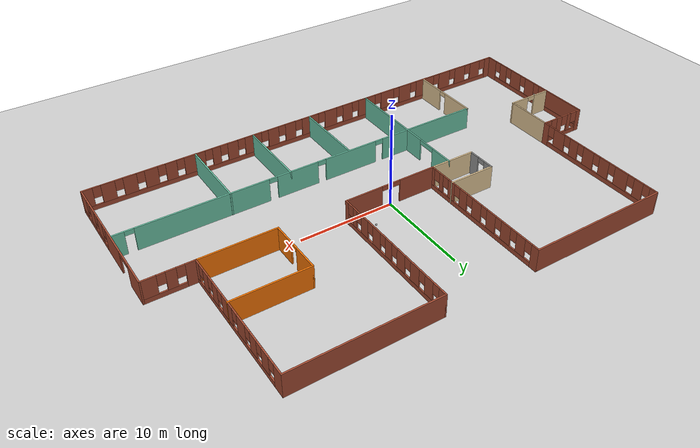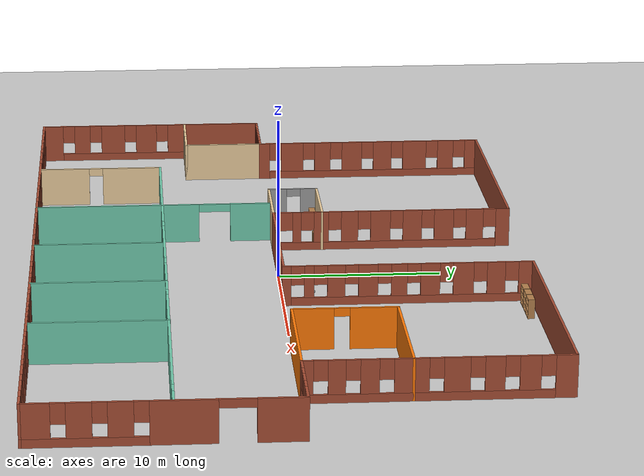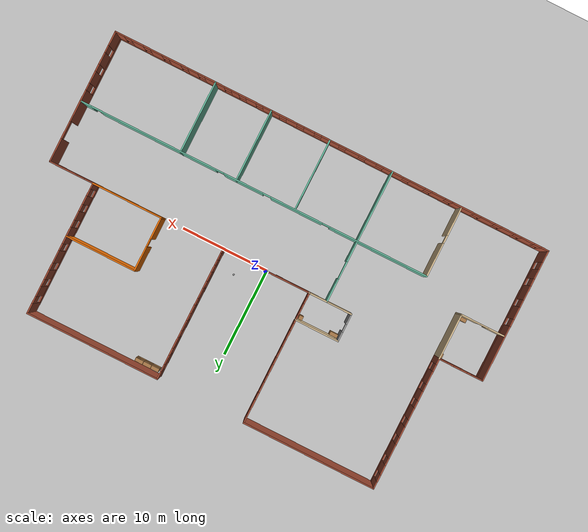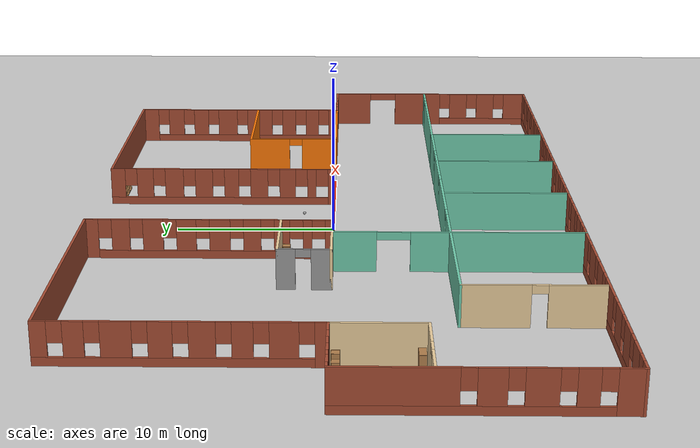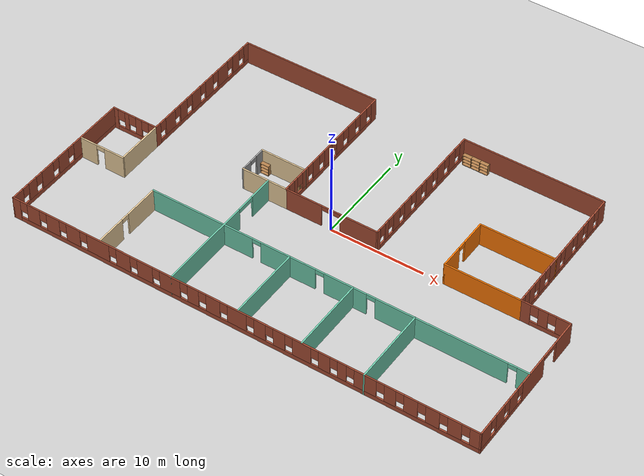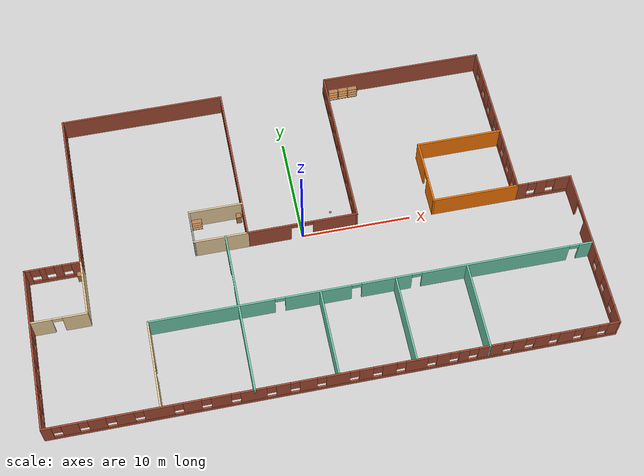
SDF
<sdf version="1.7">
 <world name="default">
  <light name="sun" type="directional">
   <pose>0 0 10 0 -0 0</pose>
   <diffuse>0.8 0.8 0.8 1</diffuse>
   <specular>0.2 0.2 0.2 1</specular>
   <attenuation>
    <range>1000</range>
    <constant>0.9</constant>
    <linear>0.01</linear>
    <quadratic>0.001</quadratic>
   </attenuation>
   <direction>-0.5 0.1 -0.9</direction>
   <spot><inner_angle>0</inner_angle><outer_angle>0</outer_angle><falloff>0</falloff></spot>
  </light>
  <model name="ground_plane">
   <static>1</static>
   <link name="link">
    <collision name="collision">
     <geometry><plane><normal>0 0 1</normal><size>100 100</size></plane></geometry>
     <surface><friction><ode><mu>100</mu><mu2>50</mu2></ode></friction></surface>
    </collision>
    <visual name="visual">
     <cast_shadows>0</cast_shadows>
     <geometry><plane><normal>0 0 1</normal><size>100 100</size></plane></geometry>
     <material>
      <script><uri>file://media/materials/scripts/gazebo.material</uri><name>Gazebo/Grey</name></script>
     </material>
    </visual>
   </link>
  </model>
  <gravity>0 0 -9.8</gravity>
  <magnetic_field>6e-06 2.3e-05 -4.2e-05</magnetic_field>
  <atmosphere type="adiabatic"/>
  <physics type="ode">
   <max_step_size>0.001</max_step_size>
   <real_time_factor>1</real_time_factor>
   <real_time_update_rate>1000</real_time_update_rate>
  </physics>
  <scene><ambient>0.4 0.4 0.4 1</ambient><background>0.7 0.7 0.7 1</background><shadows>1</shadows></scene>
  <spherical_coordinates>
   <surface_model>EARTH_WGS84</surface_model>
   <latitude_deg>0</latitude_deg>
   <longitude_deg>0</longitude_deg>
   <elevation>0</elevation>
   <heading_deg>0</heading_deg>
  </spherical_coordinates>
  <model name="office">
   <link name="Wall_10">
    <collision name="Wall_10_Collision">
     <geometry><box><size>15.15 0.15 2.5</size></box></geometry>
     <pose>0 0 1.25 0 -0 0</pose>
    </collision>
    <visual name="Wall_10_Visual">
     <pose>0 0 1.25 0 -0 0</pose>
     <geometry><box><size>15.15 0.15 2.5</size></box></geometry>
     <material>
      <script><uri>file://media/materials/scripts/gazebo.material</uri><name>Gazebo/Bricks</name></script>
      <ambient>1 1 1 1</ambient>
     </material>
     <meta><layer>0</layer></meta>
    </visual>
    <pose>-12.5 15 0 0 -0 0</pose>
   </link>
   <link name="Wall_12">
    <pose>-5 7.5 0 0 -0 -1.5708</pose>
    <visual name="Wall_12_Visual_0">
     <pose>-7.13632 0 1.25 0 -0 0</pose>
     <geometry><box><size>0.877356 0.15 2.5</size></box></geometry>
     <material>
      <script><uri>file://media/materials/scripts/gazebo.material</uri><name>Gazebo/Bricks</name></script>
      <ambient>1 1 1 1</ambient>
     </material>
     <meta><layer>0</layer></meta>
    </visual>
    <collision name="Wall_12_Collision_0">
     <geometry><box><size>0.877356 0.15 2.5</size></box></geometry>
     <pose>-7.13632 0 1.25 0 -0 0</pose>
    </collision>
    <visual name="Wall_12_Visual_1">
     <pose>0.438678 0 0.25 0 -0 0</pose>
     <geometry><box><size>14.2726 0.15 0.5</size></box></geometry>
     <material>
      <script><uri>file://media/materials/scripts/gazebo.material</uri><name>Gazebo/Bricks</name></script>
      <ambient>1 1 1 1</ambient>
     </material>
     <meta><layer>0</layer></meta>
    </visual>
    <collision name="Wall_12_Collision_1">
     <geometry><box><size>14.2726 0.15 0.5</size></box></geometry>
     <pose>0.438678 0 0.25 0 -0 0</pose>
    </collision>
    <visual name="Wall_12_Visual_2">
     <pose>-5.34792 0 1.5 0 -0 0</pose>
     <geometry><box><size>1.09946 0.15 2</size></box></geometry>
     <material>
      <script><uri>file://media/materials/scripts/gazebo.material</uri><name>Gazebo/Bricks</name></script>
      <ambient>1 1 1 1</ambient>
     </material>
     <meta><layer>0</layer></meta>
    </visual>
    <collision name="Wall_12_Collision_2">
     <geometry><box><size>1.09946 0.15 2</size></box></geometry>
     <pose>-5.34792 0 1.5 0 -0 0</pose>
    </collision>
    <visual name="Wall_12_Visual_3">
     <pose>-3.37974 0 1.5 0 -0 0</pose>
     <geometry><box><size>1.2369 0.15 2</size></box></geometry>
     <material>
      <script><uri>file://media/materials/scripts/gazebo.material</uri><name>Gazebo/Bricks</name></script>
      <ambient>1 1 1 1</ambient>
     </material>
     <meta><layer>0</layer></meta>
    </visual>
    <collision name="Wall_12_Collision_3">
     <geometry><box><size>1.2369 0.15 2</size></box></geometry>
     <pose>-3.37974 0 1.5 0 -0 0</pose>
    </collision>
    <visual name="Wall_12_Visual_4">
     <pose>-1.35847 0 1.5 0 -0 0</pose>
     <geometry><box><size>1.20564 0.15 2</size></box></geometry>
     <material>
      <script><uri>file://media/materials/scripts/gazebo.material</uri><name>Gazebo/Bricks</name></script>
      <ambient>1 1 1 1</ambient>
     </material>
     <meta><layer>0</layer></meta>
    </visual>
    <collision name="Wall_12_Collision_4">
     <geometry><box><size>1.20564 0.15 2</size></box></geometry>
     <pose>-1.35847 0 1.5 0 -0 0</pose>
    </collision>
    <visual name="Wall_12_Visual_5">
     <pose>0.676661 0 1.5 0 -0 0</pose>
     <geometry><box><size>1.26463 0.15 2</size></box></geometry>
     <material>
      <script><uri>file://media/materials/scripts/gazebo.material</uri><name>Gazebo/Bricks</name></script>
      <ambient>1 1 1 1</ambient>
     </material>
     <meta><layer>0</layer></meta>
    </visual>
    <collision name="Wall_12_Collision_5">
     <geometry><box><size>1.26463 0.15 2</size></box></geometry>
     <pose>0.676661 0 1.5 0 -0 0</pose>
    </collision>
    <visual name="Wall_12_Visual_6">
     <pose>2.64221 0 1.5 0 -0 0</pose>
     <geometry><box><size>1.06646 0.15 2</size></box></geometry>
     <material>
      <script><uri>file://media/materials/scripts/gazebo.material</uri><name>Gazebo/Bricks</name></script>
      <ambient>1 1 1 1</ambient>
     </material>
     <meta><layer>0</layer></meta>
    </visual>
    <collision name="Wall_12_Collision_6">
     <geometry><box><size>1.06646 0.15 2</size></box></geometry>
     <pose>2.64221 0 1.5 0 -0 0</pose>
    </collision>
    <visual name="Wall_12_Visual_7">
     <pose>4.44911 0 1.5 0 -0 0</pose>
     <geometry><box><size>0.947358 0.15 2</size></box></geometry>
     <material>
      <script><uri>file://media/materials/scripts/gazebo.material</uri><name>Gazebo/Bricks</name></script>
      <ambient>1 1 1 1</ambient>
     </material>
     <meta><layer>0</layer></meta>
    </visual>
    <collision name="Wall_12_Collision_7">
     <geometry><box><size>0.947358 0.15 2</size></box></geometry>
     <pose>4.44911 0 1.5 0 -0 0</pose>
    </collision>
    <visual name="Wall_12_Visual_8">
     <pose>5.99734 0 1.5 0 -0 0</pose>
     <geometry><box><size>0.549094 0.15 2</size></box></geometry>
     <material>
      <script><uri>file://media/materials/scripts/gazebo.material</uri><name>Gazebo/Bricks</name></script>
      <ambient>1 1 1 1</ambient>
     </material>
     <meta><layer>0</layer></meta>
    </visual>
    <collision name="Wall_12_Collision_8">
     <geometry><box><size>0.549094 0.15 2</size></box></geometry>
     <pose>5.99734 0 1.5 0 -0 0</pose>
    </collision>
    <visual name="Wall_12_Visual_9">
     <pose>7.32344 0 1.5 0 -0 0</pose>
     <geometry><box><size>0.503112 0.15 2</size></box></geometry>
     <material>
      <script><uri>file://media/materials/scripts/gazebo.material</uri><name>Gazebo/Bricks</name></script>
      <ambient>1 1 1 1</ambient>
     </material>
     <meta><layer>0</layer></meta>
    </visual>
    <collision name="Wall_12_Collision_9">
     <geometry><box><size>0.503112 0.15 2</size></box></geometry>
     <pose>7.32344 0 1.5 0 -0 0</pose>
    </collision>
    <visual name="Wall_12_Visual_10">
     <pose>-6.29764 0 1.9 0 -0 0</pose>
     <geometry><box><size>0.8 0.15 1.2</size></box></geometry>
     <material>
      <script><uri>file://media/materials/scripts/gazebo.material</uri><name>Gazebo/Bricks</name></script>
      <ambient>1 1 1 1</ambient>
     </material>
     <meta><layer>0</layer></meta>
    </visual>
    <collision name="Wall_12_Collision_10">
     <geometry><box><size>0.8 0.15 1.2</size></box></geometry>
     <pose>-6.29764 0 1.9 0 -0 0</pose>
    </collision>
    <visual name="Wall_12_Visual_11">
     <pose>-4.39819 0 1.9 0 -0 0</pose>
     <geometry><box><size>0.8 0.15 1.2</size></box></geometry>
     <material>
      <script><uri>file://media/materials/scripts/gazebo.material</uri><name>Gazebo/Bricks</name></script>
      <ambient>1 1 1 1</ambient>
     </material>
     <meta><layer>0</layer></meta>
    </visual>
    <collision name="Wall_12_Collision_11">
     <geometry><box><size>0.8 0.15 1.2</size></box></geometry>
     <pose>-4.39819 0 1.9 0 -0 0</pose>
    </collision>
    <visual name="Wall_12_Visual_12">
     <pose>-2.36129 0 1.9 0 -0 0</pose>
     <geometry><box><size>0.8 0.15 1.2</size></box></geometry>
     <material>
      <script><uri>file://media/materials/scripts/gazebo.material</uri><name>Gazebo/Bricks</name></script>
      <ambient>1 1 1 1</ambient>
     </material>
     <meta><layer>0</layer></meta>
    </visual>
    <collision name="Wall_12_Collision_12">
     <geometry><box><size>0.8 0.15 1.2</size></box></geometry>
     <pose>-2.36129 0 1.9 0 -0 0</pose>
    </collision>
    <visual name="Wall_12_Visual_13">
     <pose>-0.355653 0 1.9 0 -0 0</pose>
     <geometry><box><size>0.8 0.15 1.2</size></box></geometry>
     <material>
      <script><uri>file://media/materials/scripts/gazebo.material</uri><name>Gazebo/Bricks</name></script>
      <ambient>1 1 1 1</ambient>
     </material>
     <meta><layer>0</layer></meta>
    </visual>
    <collision name="Wall_12_Collision_13">
     <geometry><box><size>0.8 0.15 1.2</size></box></geometry>
     <pose>-0.355653 0 1.9 0 -0 0</pose>
    </collision>
    <visual name="Wall_12_Visual_14">
     <pose>1.70897 0 1.9 0 -0 0</pose>
     <geometry><box><size>0.8 0.15 1.2</size></box></geometry>
     <material>
      <script><uri>file://media/materials/scripts/gazebo.material</uri><name>Gazebo/Bricks</name></script>
      <ambient>1 1 1 1</ambient>
     </material>
     <meta><layer>0</layer></meta>
    </visual>
    <collision name="Wall_12_Collision_14">
     <geometry><box><size>0.8 0.15 1.2</size></box></geometry>
     <pose>1.70897 0 1.9 0 -0 0</pose>
    </collision>
    <visual name="Wall_12_Visual_15">
     <pose>3.57544 0 1.9 0 -0 0</pose>
     <geometry><box><size>0.8 0.15 1.2</size></box></geometry>
     <material>
      <script><uri>file://media/materials/scripts/gazebo.material</uri><name>Gazebo/Bricks</name></script>
      <ambient>1 1 1 1</ambient>
     </material>
     <meta><layer>0</layer></meta>
    </visual>
    <collision name="Wall_12_Collision_15">
     <geometry><box><size>0.8 0.15 1.2</size></box></geometry>
     <pose>3.57544 0 1.9 0 -0 0</pose>
    </collision>
    <visual name="Wall_12_Visual_16">
     <pose>5.32279 0 1.9 0 -0 0</pose>
     <geometry><box><size>0.8 0.15 1.2</size></box></geometry>
     <material>
      <script><uri>file://media/materials/scripts/gazebo.material</uri><name>Gazebo/Bricks</name></script>
      <ambient>1 1 1 1</ambient>
     </material>
     <meta><layer>0</layer></meta>
    </visual>
    <collision name="Wall_12_Collision_16">
     <geometry><box><size>0.8 0.15 1.2</size></box></geometry>
     <pose>5.32279 0 1.9 0 -0 0</pose>
    </collision>
    <visual name="Wall_12_Visual_17">
     <pose>6.67189 0 1.9 0 -0 0</pose>
     <geometry><box><size>0.8 0.15 1.2</size></box></geometry>
     <material>
      <script><uri>file://media/materials/scripts/gazebo.material</uri><name>Gazebo/Bricks</name></script>
      <ambient>1 1 1 1</ambient>
     </material>
     <meta><layer>0</layer></meta>
    </visual>
    <collision name="Wall_12_Collision_17">
     <geometry><box><size>0.8 0.15 1.2</size></box></geometry>
     <pose>6.67189 0 1.9 0 -0 0</pose>
    </collision>
   </link>
   <link name="Wall_14">
    <visual name="Wall_14_Visual_0">
     <pose>-3.05414 0 1.25 0 -0 0</pose>
     <geometry><box><size>4.04172 0.15 2.5</size></box></geometry>
     <material>
      <script><uri>file://media/materials/scripts/gazebo.material</uri><name>Gazebo/Bricks</name></script>
      <ambient>1 1 1 1</ambient>
     </material>
     <meta><layer>0</layer></meta>
    </visual>
    <collision name="Wall_14_Collision_0">
     <geometry><box><size>4.04172 0.15 2.5</size></box></geometry>
     <pose>-3.05414 0 1.25 0 -0 0</pose>
    </collision>
    <visual name="Wall_14_Visual_1">
     <pose>3.02086 0 1.25 0 -0 0</pose>
     <geometry><box><size>4.10827 0.15 2.5</size></box></geometry>
     <material>
      <script><uri>file://media/materials/scripts/gazebo.material</uri><name>Gazebo/Bricks</name></script>
      <ambient>1 1 1 1</ambient>
     </material>
     <meta><layer>0</layer></meta>
    </visual>
    <collision name="Wall_14_Collision_1">
     <geometry><box><size>4.10827 0.15 2.5</size></box></geometry>
     <pose>3.02086 0 1.25 0 -0 0</pose>
    </collision>
    <visual name="Wall_14_Visual_2">
     <pose>-0.033275 0 2.25 0 -0 0</pose>
     <geometry><box><size>2 0.15 0.5</size></box></geometry>
     <material>
      <script><uri>file://media/materials/scripts/gazebo.material</uri><name>Gazebo/Bricks</name></script>
      <ambient>1 1 1 1</ambient>
     </material>
     <meta><layer>0</layer></meta>
    </visual>
    <collision name="Wall_14_Collision_2">
     <geometry><box><size>2 0.15 0.5</size></box></geometry>
     <pose>-0.033275 0 2.25 0 -0 0</pose>
    </collision>
   </link>
   <link name="Wall_16">
    <pose>5 7.5 0 0 -0 1.5708</pose>
    <visual name="Wall_16_Visual_0">
     <pose>-7.31594 0 1.25 0 -0 0</pose>
     <geometry><box><size>0.518129 0.15 2.5</size></box></geometry>
     <material>
      <script><uri>file://media/materials/scripts/gazebo.material</uri><name>Gazebo/Bricks</name></script>
      <ambient>1 1 1 1</ambient>
     </material>
     <meta><layer>0</layer></meta>
    </visual>
    <collision name="Wall_16_Collision_0">
     <geometry><box><size>0.518129 0.15 2.5</size></box></geometry>
     <pose>-7.31594 0 1.25 0 -0 0</pose>
    </collision>
    <visual name="Wall_16_Visual_1">
     <pose>0.259064 0 0.25 0 -0 0</pose>
     <geometry><box><size>14.6319 0.15 0.5</size></box></geometry>
     <material>
      <script><uri>file://media/materials/scripts/gazebo.material</uri><name>Gazebo/Bricks</name></script>
      <ambient>1 1 1 1</ambient>
     </material>
     <meta><layer>0</layer></meta>
    </visual>
    <collision name="Wall_16_Collision_1">
     <geometry><box><size>14.6319 0.15 0.5</size></box></geometry>
     <pose>0.259064 0 0.25 0 -0 0</pose>
    </collision>
    <visual name="Wall_16_Visual_2">
     <pose>-5.96546 0 1.5 0 -0 0</pose>
     <geometry><box><size>0.582822 0.15 2</size></box></geometry>
     <material>
      <script><uri>file://media/materials/scripts/gazebo.material</uri><name>Gazebo/Bricks</name></script>
      <ambient>1 1 1 1</ambient>
     </material>
     <meta><layer>0</layer></meta>
    </visual>
    <collision name="Wall_16_Collision_2">
     <geometry><box><size>0.582822 0.15 2</size></box></geometry>
     <pose>-5.96546 0 1.5 0 -0 0</pose>
    </collision>
    <visual name="Wall_16_Visual_3">
     <pose>-4.34021 0 1.5 0 -0 0</pose>
     <geometry><box><size>1.06767 0.15 2</size></box></geometry>
     <material>
      <script><uri>file://media/materials/scripts/gazebo.material</uri><name>Gazebo/Bricks</name></script>
      <ambient>1 1 1 1</ambient>
     </material>
     <meta><layer>0</layer></meta>
    </visual>
    <collision name="Wall_16_Collision_3">
     <geometry><box><size>1.06767 0.15 2</size></box></geometry>
     <pose>-4.34021 0 1.5 0 -0 0</pose>
    </collision>
    <visual name="Wall_16_Visual_4">
     <pose>-2.42273 0 1.5 0 -0 0</pose>
     <geometry><box><size>1.16729 0.15 2</size></box></geometry>
     <material>
      <script><uri>file://media/materials/scripts/gazebo.material</uri><name>Gazebo/Bricks</name></script>
      <ambient>1 1 1 1</ambient>
     </material>
     <meta><layer>0</layer></meta>
    </visual>
    <collision name="Wall_16_Collision_4">
     <geometry><box><size>1.16729 0.15 2</size></box></geometry>
     <pose>-2.42273 0 1.5 0 -0 0</pose>
    </collision>
    <visual name="Wall_16_Visual_5">
     <pose>-0.557195 0 1.5 0 -0 0</pose>
     <geometry><box><size>0.963782 0.15 2</size></box></geometry>
     <material>
      <script><uri>file://media/materials/scripts/gazebo.material</uri><name>Gazebo/Bricks</name></script>
      <ambient>1 1 1 1</ambient>
     </material>
     <meta><layer>0</layer></meta>
    </visual>
    <collision name="Wall_16_Collision_5">
     <geometry><box><size>0.963782 0.15 2</size></box></geometry>
     <pose>-0.557195 0 1.5 0 -0 0</pose>
    </collision>
    <visual name="Wall_16_Visual_6">
     <pose>1.30834 0 1.5 0 -0 0</pose>
     <geometry><box><size>1.16729 0.15 2</size></box></geometry>
     <material>
      <script><uri>file://media/materials/scripts/gazebo.material</uri><name>Gazebo/Bricks</name></script>
      <ambient>1 1 1 1</ambient>
     </material>
     <meta><layer>0</layer></meta>
    </visual>
    <collision name="Wall_16_Collision_6">
     <geometry><box><size>1.16729 0.15 2</size></box></geometry>
     <pose>1.30834 0 1.5 0 -0 0</pose>
    </collision>
    <visual name="Wall_16_Visual_7">
     <pose>3.30956 0 1.5 0 -0 0</pose>
     <geometry><box><size>1.23513 0.15 2</size></box></geometry>
     <material>
      <script><uri>file://media/materials/scripts/gazebo.material</uri><name>Gazebo/Bricks</name></script>
      <ambient>1 1 1 1</ambient>
     </material>
     <meta><layer>0</layer></meta>
    </visual>
    <collision name="Wall_16_Collision_7">
     <geometry><box><size>1.23513 0.15 2</size></box></geometry>
     <pose>3.30956 0 1.5 0 -0 0</pose>
    </collision>
    <visual name="Wall_16_Visual_8">
     <pose>5.27685 0 1.5 0 -0 0</pose>
     <geometry><box><size>1.09946 0.15 2</size></box></geometry>
     <material>
      <script><uri>file://media/materials/scripts/gazebo.material</uri><name>Gazebo/Bricks</name></script>
      <ambient>1 1 1 1</ambient>
     </material>
     <meta><layer>0</layer></meta>
    </visual>
    <collision name="Wall_16_Collision_8">
     <geometry><box><size>1.09946 0.15 2</size></box></geometry>
     <pose>5.27685 0 1.5 0 -0 0</pose>
    </collision>
    <visual name="Wall_16_Visual_9">
     <pose>7.10079 0 1.5 0 -0 0</pose>
     <geometry><box><size>0.948419 0.15 2</size></box></geometry>
     <material>
      <script><uri>file://media/materials/scripts/gazebo.material</uri><name>Gazebo/Bricks</name></script>
      <ambient>1 1 1 1</ambient>
     </material>
     <meta><layer>0</layer></meta>
    </visual>
    <collision name="Wall_16_Collision_9">
     <geometry><box><size>0.948419 0.15 2</size></box></geometry>
     <pose>7.10079 0 1.5 0 -0 0</pose>
    </collision>
    <visual name="Wall_16_Visual_10">
     <pose>-6.65687 0 1.9 0 -0 0</pose>
     <geometry><box><size>0.8 0.15 1.2</size></box></geometry>
     <material>
      <script><uri>file://media/materials/scripts/gazebo.material</uri><name>Gazebo/Bricks</name></script>
      <ambient>1 1 1 1</ambient>
     </material>
     <meta><layer>0</layer></meta>
    </visual>
    <collision name="Wall_16_Collision_10">
     <geometry><box><size>0.8 0.15 1.2</size></box></geometry>
     <pose>-6.65687 0 1.9 0 -0 0</pose>
    </collision>
    <visual name="Wall_16_Visual_11">
     <pose>-5.27405 0 1.9 0 -0 0</pose>
     <geometry><box><size>0.8 0.15 1.2</size></box></geometry>
     <material>
      <script><uri>file://media/materials/scripts/gazebo.material</uri><name>Gazebo/Bricks</name></script>
      <ambient>1 1 1 1</ambient>
     </material>
     <meta><layer>0</layer></meta>
    </visual>
    <collision name="Wall_16_Collision_11">
     <geometry><box><size>0.8 0.15 1.2</size></box></geometry>
     <pose>-5.27405 0 1.9 0 -0 0</pose>
    </collision>
    <visual name="Wall_16_Visual_12">
     <pose>-3.40638 0 1.9 0 -0 0</pose>
     <geometry><box><size>0.8 0.15 1.2</size></box></geometry>
     <material>
      <script><uri>file://media/materials/scripts/gazebo.material</uri><name>Gazebo/Bricks</name></script>
      <ambient>1 1 1 1</ambient>
     </material>
     <meta><layer>0</layer></meta>
    </visual>
    <collision name="Wall_16_Collision_12">
     <geometry><box><size>0.8 0.15 1.2</size></box></geometry>
     <pose>-3.40638 0 1.9 0 -0 0</pose>
    </collision>
    <visual name="Wall_16_Visual_13">
     <pose>-1.43908 0 1.9 0 -0 0</pose>
     <geometry><box><size>0.8 0.15 1.2</size></box></geometry>
     <material>
      <script><uri>file://media/materials/scripts/gazebo.material</uri><name>Gazebo/Bricks</name></script>
      <ambient>1 1 1 1</ambient>
     </material>
     <meta><layer>0</layer></meta>
    </visual>
    <collision name="Wall_16_Collision_13">
     <geometry><box><size>0.8 0.15 1.2</size></box></geometry>
     <pose>-1.43908 0 1.9 0 -0 0</pose>
    </collision>
    <visual name="Wall_16_Visual_14">
     <pose>0.324696 0 1.9 0 -0 0</pose>
     <geometry><box><size>0.8 0.15 1.2</size></box></geometry>
     <material>
      <script><uri>file://media/materials/scripts/gazebo.material</uri><name>Gazebo/Bricks</name></script>
      <ambient>1 1 1 1</ambient>
     </material>
     <meta><layer>0</layer></meta>
    </visual>
    <collision name="Wall_16_Collision_14">
     <geometry><box><size>0.8 0.15 1.2</size></box></geometry>
     <pose>0.324696 0 1.9 0 -0 0</pose>
    </collision>
    <visual name="Wall_16_Visual_15">
     <pose>2.29199 0 1.9 0 -0 0</pose>
     <geometry><box><size>0.8 0.15 1.2</size></box></geometry>
     <material>
      <script><uri>file://media/materials/scripts/gazebo.material</uri><name>Gazebo/Bricks</name></script>
      <ambient>1 1 1 1</ambient>
     </material>
     <meta><layer>0</layer></meta>
    </visual>
    <collision name="Wall_16_Collision_15">
     <geometry><box><size>0.8 0.15 1.2</size></box></geometry>
     <pose>2.29199 0 1.9 0 -0 0</pose>
    </collision>
    <visual name="Wall_16_Visual_16">
     <pose>4.32712 0 1.9 0 -0 0</pose>
     <geometry><box><size>0.8 0.15 1.2</size></box></geometry>
     <material>
      <script><uri>file://media/materials/scripts/gazebo.material</uri><name>Gazebo/Bricks</name></script>
      <ambient>1 1 1 1</ambient>
     </material>
     <meta><layer>0</layer></meta>
    </visual>
    <collision name="Wall_16_Collision_16">
     <geometry><box><size>0.8 0.15 1.2</size></box></geometry>
     <pose>4.32712 0 1.9 0 -0 0</pose>
    </collision>
    <visual name="Wall_16_Visual_17">
     <pose>6.22658 0 1.9 0 -0 0</pose>
     <geometry><box><size>0.8 0.15 1.2</size></box></geometry>
     <material>
      <script><uri>file://media/materials/scripts/gazebo.material</uri><name>Gazebo/Bricks</name></script>
      <ambient>1 1 1 1</ambient>
     </material>
     <meta><layer>0</layer></meta>
    </visual>
    <collision name="Wall_16_Collision_17">
     <geometry><box><size>0.8 0.15 1.2</size></box></geometry>
     <pose>6.22658 0 1.9 0 -0 0</pose>
    </collision>
   </link>
   <link name="Wall_2">
    <pose>0 -15 0 0 -0 0</pose>
    <visual name="Wall_2_Visual_0">
     <pose>-24.6249 0 1.25 0 -0 0</pose>
     <geometry><box><size>0.900286 0.15 2.5</size></box></geometry>
     <material>
      <script><uri>file://media/materials/scripts/gazebo.material</uri><name>Gazebo/Bricks</name></script>
      <ambient>1 1 1 1</ambient>
     </material>
     <meta><layer>0</layer></meta>
    </visual>
    <collision name="Wall_2_Collision_0">
     <geometry><box><size>0.900286 0.15 2.5</size></box></geometry>
     <pose>-24.6249 0 1.25 0 -0 0</pose>
    </collision>
    <visual name="Wall_2_Visual_1">
     <pose>0.450143 0 0.25 0 -0 0</pose>
     <geometry><box><size>49.2497 0.15 0.5</size></box></geometry>
     <material>
      <script><uri>file://media/materials/scripts/gazebo.material</uri><name>Gazebo/Bricks</name></script>
      <ambient>1 1 1 1</ambient>
     </material>
     <meta><layer>0</layer></meta>
    </visual>
    <collision name="Wall_2_Collision_1">
     <geometry><box><size>49.2497 0.15 0.5</size></box></geometry>
     <pose>0.450143 0 0.25 0 -0 0</pose>
    </collision>
    <visual name="Wall_2_Visual_2">
     <pose>-22.6554 0 1.5 0 -0 0</pose>
     <geometry><box><size>1.43865 0.15 2</size></box></geometry>
     <material>
      <script><uri>file://media/materials/scripts/gazebo.material</uri><name>Gazebo/Bricks</name></script>
      <ambient>1 1 1 1</ambient>
     </material>
     <meta><layer>0</layer></meta>
    </visual>
    <collision name="Wall_2_Collision_2">
     <geometry><box><size>1.43865 0.15 2</size></box></geometry>
     <pose>-22.6554 0 1.5 0 -0 0</pose>
    </collision>
    <visual name="Wall_2_Visual_3">
     <pose>-20.3828 0 1.5 0 -0 0</pose>
     <geometry><box><size>1.50648 0.15 2</size></box></geometry>
     <material>
      <script><uri>file://media/materials/scripts/gazebo.material</uri><name>Gazebo/Bricks</name></script>
      <ambient>1 1 1 1</ambient>
     </material>
     <meta><layer>0</layer></meta>
    </visual>
    <collision name="Wall_2_Collision_3">
     <geometry><box><size>1.50648 0.15 2</size></box></geometry>
     <pose>-20.3828 0 1.5 0 -0 0</pose>
    </collision>
    <visual name="Wall_2_Visual_4">
     <pose>-18.0424 0 1.5 0 -0 0</pose>
     <geometry><box><size>1.57432 0.15 2</size></box></geometry>
     <material>
      <script><uri>file://media/materials/scripts/gazebo.material</uri><name>Gazebo/Bricks</name></script>
      <ambient>1 1 1 1</ambient>
     </material>
     <meta><layer>0</layer></meta>
    </visual>
    <collision name="Wall_2_Collision_4">
     <geometry><box><size>1.57432 0.15 2</size></box></geometry>
     <pose>-18.0424 0 1.5 0 -0 0</pose>
    </collision>
    <visual name="Wall_2_Visual_5">
     <pose>-15.1932 0 1.5 0 -0 0</pose>
     <geometry><box><size>2.52405 0.15 2</size></box></geometry>
     <material>
      <script><uri>file://media/materials/scripts/gazebo.material</uri><name>Gazebo/Bricks</name></script>
      <ambient>1 1 1 1</ambient>
     </material>
     <meta><layer>0</layer></meta>
    </visual>
    <collision name="Wall_2_Collision_5">
     <geometry><box><size>2.52405 0.15 2</size></box></geometry>
     <pose>-15.1932 0 1.5 0 -0 0</pose>
    </collision>
    <visual name="Wall_2_Visual_6">
     <pose>-12.3441 0 1.5 0 -0 0</pose>
     <geometry><box><size>1.57432 0.15 2</size></box></geometry>
     <material>
      <script><uri>file://media/materials/scripts/gazebo.material</uri><name>Gazebo/Bricks</name></script>
      <ambient>1 1 1 1</ambient>
     </material>
     <meta><layer>0</layer></meta>
    </visual>
    <collision name="Wall_2_Collision_6">
     <geometry><box><size>1.57432 0.15 2</size></box></geometry>
     <pose>-12.3441 0 1.5 0 -0 0</pose>
    </collision>
    <visual name="Wall_2_Visual_7">
     <pose>-9.90189 0 1.5 0 -0 0</pose>
     <geometry><box><size>1.71 0.15 2</size></box></geometry>
     <material>
      <script><uri>file://media/materials/scripts/gazebo.material</uri><name>Gazebo/Bricks</name></script>
      <ambient>1 1 1 1</ambient>
     </material>
     <meta><layer>0</layer></meta>
    </visual>
    <collision name="Wall_2_Collision_7">
     <geometry><box><size>1.71 0.15 2</size></box></geometry>
     <pose>-9.90189 0 1.5 0 -0 0</pose>
    </collision>
    <visual name="Wall_2_Visual_8">
     <pose>-7.12054 0 1.5 0 -0 0</pose>
     <geometry><box><size>2.2527 0.15 2</size></box></geometry>
     <material>
      <script><uri>file://media/materials/scripts/gazebo.material</uri><name>Gazebo/Bricks</name></script>
      <ambient>1 1 1 1</ambient>
     </material>
     <meta><layer>0</layer></meta>
    </visual>
    <collision name="Wall_2_Collision_8">
     <geometry><box><size>2.2527 0.15 2</size></box></geometry>
     <pose>-7.12054 0 1.5 0 -0 0</pose>
    </collision>
    <visual name="Wall_2_Visual_9">
     <pose>-4.57663 0 1.5 0 -0 0</pose>
     <geometry><box><size>1.23513 0.15 2</size></box></geometry>
     <material>
      <script><uri>file://media/materials/scripts/gazebo.material</uri><name>Gazebo/Bricks</name></script>
      <ambient>1 1 1 1</ambient>
     </material>
     <meta><layer>0</layer></meta>
    </visual>
    <collision name="Wall_2_Collision_9">
     <geometry><box><size>1.23513 0.15 2</size></box></geometry>
     <pose>-4.57663 0 1.5 0 -0 0</pose>
    </collision>
    <visual name="Wall_2_Visual_10">
     <pose>-2.40582 0 1.5 0 -0 0</pose>
     <geometry><box><size>1.50648 0.15 2</size></box></geometry>
     <material>
      <script><uri>file://media/materials/scripts/gazebo.material</uri><name>Gazebo/Bricks</name></script>
      <ambient>1 1 1 1</ambient>
     </material>
     <meta><layer>0</layer></meta>
    </visual>
    <collision name="Wall_2_Collision_10">
     <geometry><box><size>1.50648 0.15 2</size></box></geometry>
     <pose>-2.40582 0 1.5 0 -0 0</pose>
    </collision>
    <visual name="Wall_2_Visual_11">
     <pose>0.172015 0 1.5 0 -0 0</pose>
     <geometry><box><size>2.04919 0.15 2</size></box></geometry>
     <material>
      <script><uri>file://media/materials/scripts/gazebo.material</uri><name>Gazebo/Bricks</name></script>
      <ambient>1 1 1 1</ambient>
     </material>
     <meta><layer>0</layer></meta>
    </visual>
    <collision name="Wall_2_Collision_11">
     <geometry><box><size>2.04919 0.15 2</size></box></geometry>
     <pose>0.172015 0 1.5 0 -0 0</pose>
    </collision>
    <visual name="Wall_2_Visual_12">
     <pose>2.61417 0 1.5 0 -0 0</pose>
     <geometry><box><size>1.23513 0.15 2</size></box></geometry>
     <material>
      <script><uri>file://media/materials/scripts/gazebo.material</uri><name>Gazebo/Bricks</name></script>
      <ambient>1 1 1 1</ambient>
     </material>
     <meta><layer>0</layer></meta>
    </visual>
    <collision name="Wall_2_Collision_12">
     <geometry><box><size>1.23513 0.15 2</size></box></geometry>
     <pose>2.61417 0 1.5 0 -0 0</pose>
    </collision>
    <visual name="Wall_2_Visual_13">
     <pose>4.64931 0 1.5 0 -0 0</pose>
     <geometry><box><size>1.23513 0.15 2</size></box></geometry>
     <material>
      <script><uri>file://media/materials/scripts/gazebo.material</uri><name>Gazebo/Bricks</name></script>
      <ambient>1 1 1 1</ambient>
     </material>
     <meta><layer>0</layer></meta>
    </visual>
    <collision name="Wall_2_Collision_13">
     <geometry><box><size>1.23513 0.15 2</size></box></geometry>
     <pose>4.64931 0 1.5 0 -0 0</pose>
    </collision>
    <visual name="Wall_2_Visual_14">
     <pose>7.02363 0 1.5 0 -0 0</pose>
     <geometry><box><size>1.91351 0.15 2</size></box></geometry>
     <material>
      <script><uri>file://media/materials/scripts/gazebo.material</uri><name>Gazebo/Bricks</name></script>
      <ambient>1 1 1 1</ambient>
     </material>
     <meta><layer>0</layer></meta>
    </visual>
    <collision name="Wall_2_Collision_14">
     <geometry><box><size>1.91351 0.15 2</size></box></geometry>
     <pose>7.02363 0 1.5 0 -0 0</pose>
    </collision>
    <visual name="Wall_2_Visual_15">
     <pose>9.36403 0 1.5 0 -0 0</pose>
     <geometry><box><size>1.16729 0.15 2</size></box></geometry>
     <material>
      <script><uri>file://media/materials/scripts/gazebo.material</uri><name>Gazebo/Bricks</name></script>
      <ambient>1 1 1 1</ambient>
     </material>
     <meta><layer>0</layer></meta>
    </visual>
    <collision name="Wall_2_Collision_15">
     <geometry><box><size>1.16729 0.15 2</size></box></geometry>
     <pose>9.36403 0 1.5 0 -0 0</pose>
    </collision>
    <visual name="Wall_2_Visual_16">
     <pose>11.1957 0 1.5 0 -0 0</pose>
     <geometry><box><size>0.895944 0.15 2</size></box></geometry>
     <material>
      <script><uri>file://media/materials/scripts/gazebo.material</uri><name>Gazebo/Bricks</name></script>
      <ambient>1 1 1 1</ambient>
     </material>
     <meta><layer>0</layer></meta>
    </visual>
    <collision name="Wall_2_Collision_16">
     <geometry><box><size>0.895944 0.15 2</size></box></geometry>
     <pose>11.1957 0 1.5 0 -0 0</pose>
    </collision>
    <visual name="Wall_2_Visual_17">
     <pose>13.57 0 1.5 0 -0 0</pose>
     <geometry><box><size>2.2527 0.15 2</size></box></geometry>
     <material>
      <script><uri>file://media/materials/scripts/gazebo.material</uri><name>Gazebo/Bricks</name></script>
      <ambient>1 1 1 1</ambient>
     </material>
     <meta><layer>0</layer></meta>
    </visual>
    <collision name="Wall_2_Collision_17">
     <geometry><box><size>2.2527 0.15 2</size></box></geometry>
     <pose>13.57 0 1.5 0 -0 0</pose>
    </collision>
    <visual name="Wall_2_Visual_18">
     <pose>16.08 0 1.5 0 -0 0</pose>
     <geometry><box><size>1.16729 0.15 2</size></box></geometry>
     <material>
      <script><uri>file://media/materials/scripts/gazebo.material</uri><name>Gazebo/Bricks</name></script>
      <ambient>1 1 1 1</ambient>
     </material>
     <meta><layer>0</layer></meta>
    </visual>
    <collision name="Wall_2_Collision_18">
     <geometry><box><size>1.16729 0.15 2</size></box></geometry>
     <pose>16.08 0 1.5 0 -0 0</pose>
    </collision>
    <visual name="Wall_2_Visual_19">
     <pose>18.149 0 1.5 0 -0 0</pose>
     <geometry><box><size>1.37081 0.15 2</size></box></geometry>
     <material>
      <script><uri>file://media/materials/scripts/gazebo.material</uri><name>Gazebo/Bricks</name></script>
      <ambient>1 1 1 1</ambient>
     </material>
     <meta><layer>0</layer></meta>
    </visual>
    <collision name="Wall_2_Collision_19">
     <geometry><box><size>1.37081 0.15 2</size></box></geometry>
     <pose>18.149 0 1.5 0 -0 0</pose>
    </collision>
    <visual name="Wall_2_Visual_20">
     <pose>20.3198 0 1.5 0 -0 0</pose>
     <geometry><box><size>1.37081 0.15 2</size></box></geometry>
     <material>
      <script><uri>file://media/materials/scripts/gazebo.material</uri><name>Gazebo/Bricks</name></script>
      <ambient>1 1 1 1</ambient>
     </material>
     <meta><layer>0</layer></meta>
    </visual>
    <collision name="Wall_2_Collision_20">
     <geometry><box><size>1.37081 0.15 2</size></box></geometry>
     <pose>20.3198 0 1.5 0 -0 0</pose>
    </collision>
    <visual name="Wall_2_Visual_21">
     <pose>22.4906 0 1.5 0 -0 0</pose>
     <geometry><box><size>1.37081 0.15 2</size></box></geometry>
     <material>
      <script><uri>file://media/materials/scripts/gazebo.material</uri><name>Gazebo/Bricks</name></script>
      <ambient>1 1 1 1</ambient>
     </material>
     <meta><layer>0</layer></meta>
    </visual>
    <collision name="Wall_2_Collision_21">
     <geometry><box><size>1.37081 0.15 2</size></box></geometry>
     <pose>22.4906 0 1.5 0 -0 0</pose>
    </collision>
    <visual name="Wall_2_Visual_22">
     <pose>24.5255 0 1.5 0 -0 0</pose>
     <geometry><box><size>1.09896 0.15 2</size></box></geometry>
     <material>
      <script><uri>file://media/materials/scripts/gazebo.material</uri><name>Gazebo/Bricks</name></script>
      <ambient>1 1 1 1</ambient>
     </material>
     <meta><layer>0</layer></meta>
    </visual>
    <collision name="Wall_2_Collision_22">
     <geometry><box><size>1.09896 0.15 2</size></box></geometry>
     <pose>24.5255 0 1.5 0 -0 0</pose>
    </collision>
    <visual name="Wall_2_Visual_23">
     <pose>-23.7747 0 1.9 0 -0 0</pose>
     <geometry><box><size>0.8 0.15 1.2</size></box></geometry>
     <material>
      <script><uri>file://media/materials/scripts/gazebo.material</uri><name>Gazebo/Bricks</name></script>
      <ambient>1 1 1 1</ambient>
     </material>
     <meta><layer>0</layer></meta>
    </visual>
    <collision name="Wall_2_Collision_23">
     <geometry><box><size>0.8 0.15 1.2</size></box></geometry>
     <pose>-23.7747 0 1.9 0 -0 0</pose>
    </collision>
    <visual name="Wall_2_Visual_24">
     <pose>-21.5361 0 1.9 0 -0 0</pose>
     <geometry><box><size>0.8 0.15 1.2</size></box></geometry>
     <material>
      <script><uri>file://media/materials/scripts/gazebo.material</uri><name>Gazebo/Bricks</name></script>
      <ambient>1 1 1 1</ambient>
     </material>
     <meta><layer>0</layer></meta>
    </visual>
    <collision name="Wall_2_Collision_24">
     <geometry><box><size>0.8 0.15 1.2</size></box></geometry>
     <pose>-21.5361 0 1.9 0 -0 0</pose>
    </collision>
    <visual name="Wall_2_Visual_25">
     <pose>-19.2296 0 1.9 0 -0 0</pose>
     <geometry><box><size>0.8 0.15 1.2</size></box></geometry>
     <material>
      <script><uri>file://media/materials/scripts/gazebo.material</uri><name>Gazebo/Bricks</name></script>
      <ambient>1 1 1 1</ambient>
     </material>
     <meta><layer>0</layer></meta>
    </visual>
    <collision name="Wall_2_Collision_25">
     <geometry><box><size>0.8 0.15 1.2</size></box></geometry>
     <pose>-19.2296 0 1.9 0 -0 0</pose>
    </collision>
    <visual name="Wall_2_Visual_26">
     <pose>-16.8553 0 1.9 0 -0 0</pose>
     <geometry><box><size>0.8 0.15 1.2</size></box></geometry>
     <material>
      <script><uri>file://media/materials/scripts/gazebo.material</uri><name>Gazebo/Bricks</name></script>
      <ambient>1 1 1 1</ambient>
     </material>
     <meta><layer>0</layer></meta>
    </visual>
    <collision name="Wall_2_Collision_26">
     <geometry><box><size>0.8 0.15 1.2</size></box></geometry>
     <pose>-16.8553 0 1.9 0 -0 0</pose>
    </collision>
    <visual name="Wall_2_Visual_27">
     <pose>-13.5312 0 1.9 0 -0 0</pose>
     <geometry><box><size>0.8 0.15 1.2</size></box></geometry>
     <material>
      <script><uri>file://media/materials/scripts/gazebo.material</uri><name>Gazebo/Bricks</name></script>
      <ambient>1 1 1 1</ambient>
     </material>
     <meta><layer>0</layer></meta>
    </visual>
    <collision name="Wall_2_Collision_27">
     <geometry><box><size>0.8 0.15 1.2</size></box></geometry>
     <pose>-13.5312 0 1.9 0 -0 0</pose>
    </collision>
    <visual name="Wall_2_Visual_28">
     <pose>-11.1569 0 1.9 0 -0 0</pose>
     <geometry><box><size>0.8 0.15 1.2</size></box></geometry>
     <material>
      <script><uri>file://media/materials/scripts/gazebo.material</uri><name>Gazebo/Bricks</name></script>
      <ambient>1 1 1 1</ambient>
     </material>
     <meta><layer>0</layer></meta>
    </visual>
    <collision name="Wall_2_Collision_28">
     <geometry><box><size>0.8 0.15 1.2</size></box></geometry>
     <pose>-11.1569 0 1.9 0 -0 0</pose>
    </collision>
    <visual name="Wall_2_Visual_29">
     <pose>-8.64689 0 1.9 0 -0 0</pose>
     <geometry><box><size>0.8 0.15 1.2</size></box></geometry>
     <material>
      <script><uri>file://media/materials/scripts/gazebo.material</uri><name>Gazebo/Bricks</name></script>
      <ambient>1 1 1 1</ambient>
     </material>
     <meta><layer>0</layer></meta>
    </visual>
    <collision name="Wall_2_Collision_29">
     <geometry><box><size>0.8 0.15 1.2</size></box></geometry>
     <pose>-8.64689 0 1.9 0 -0 0</pose>
    </collision>
    <visual name="Wall_2_Visual_30">
     <pose>-5.59419 0 1.9 0 -0 0</pose>
     <geometry><box><size>0.8 0.15 1.2</size></box></geometry>
     <material>
      <script><uri>file://media/materials/scripts/gazebo.material</uri><name>Gazebo/Bricks</name></script>
      <ambient>1 1 1 1</ambient>
     </material>
     <meta><layer>0</layer></meta>
    </visual>
    <collision name="Wall_2_Collision_30">
     <geometry><box><size>0.8 0.15 1.2</size></box></geometry>
     <pose>-5.59419 0 1.9 0 -0 0</pose>
    </collision>
    <visual name="Wall_2_Visual_31">
     <pose>-3.55906 0 1.9 0 -0 0</pose>
     <geometry><box><size>0.8 0.15 1.2</size></box></geometry>
     <material>
      <script><uri>file://media/materials/scripts/gazebo.material</uri><name>Gazebo/Bricks</name></script>
      <ambient>1 1 1 1</ambient>
     </material>
     <meta><layer>0</layer></meta>
    </visual>
    <collision name="Wall_2_Collision_31">
     <geometry><box><size>0.8 0.15 1.2</size></box></geometry>
     <pose>-3.55906 0 1.9 0 -0 0</pose>
    </collision>
    <visual name="Wall_2_Visual_32">
     <pose>-1.25258 0 1.9 0 -0 0</pose>
     <geometry><box><size>0.8 0.15 1.2</size></box></geometry>
     <material>
      <script><uri>file://media/materials/scripts/gazebo.material</uri><name>Gazebo/Bricks</name></script>
      <ambient>1 1 1 1</ambient>
     </material>
     <meta><layer>0</layer></meta>
    </visual>
    <collision name="Wall_2_Collision_32">
     <geometry><box><size>0.8 0.15 1.2</size></box></geometry>
     <pose>-1.25258 0 1.9 0 -0 0</pose>
    </collision>
    <visual name="Wall_2_Visual_33">
     <pose>1.59661 0 1.9 0 -0 0</pose>
     <geometry><box><size>0.8 0.15 1.2</size></box></geometry>
     <material>
      <script><uri>file://media/materials/scripts/gazebo.material</uri><name>Gazebo/Bricks</name></script>
      <ambient>1 1 1 1</ambient>
     </material>
     <meta><layer>0</layer></meta>
    </visual>
    <collision name="Wall_2_Collision_33">
     <geometry><box><size>0.8 0.15 1.2</size></box></geometry>
     <pose>1.59661 0 1.9 0 -0 0</pose>
    </collision>
    <visual name="Wall_2_Visual_34">
     <pose>3.63174 0 1.9 0 -0 0</pose>
     <geometry><box><size>0.8 0.15 1.2</size></box></geometry>
     <material>
      <script><uri>file://media/materials/scripts/gazebo.material</uri><name>Gazebo/Bricks</name></script>
      <ambient>1 1 1 1</ambient>
     </material>
     <meta><layer>0</layer></meta>
    </visual>
    <collision name="Wall_2_Collision_34">
     <geometry><box><size>0.8 0.15 1.2</size></box></geometry>
     <pose>3.63174 0 1.9 0 -0 0</pose>
    </collision>
    <visual name="Wall_2_Visual_35">
     <pose>5.66687 0 1.9 0 -0 0</pose>
     <geometry><box><size>0.8 0.15 1.2</size></box></geometry>
     <material>
      <script><uri>file://media/materials/scripts/gazebo.material</uri><name>Gazebo/Bricks</name></script>
      <ambient>1 1 1 1</ambient>
     </material>
     <meta><layer>0</layer></meta>
    </visual>
    <collision name="Wall_2_Collision_35">
     <geometry><box><size>0.8 0.15 1.2</size></box></geometry>
     <pose>5.66687 0 1.9 0 -0 0</pose>
    </collision>
    <visual name="Wall_2_Visual_36">
     <pose>8.38038 0 1.9 0 -0 0</pose>
     <geometry><box><size>0.8 0.15 1.2</size></box></geometry>
     <material>
      <script><uri>file://media/materials/scripts/gazebo.material</uri><name>Gazebo/Bricks</name></script>
      <ambient>1 1 1 1</ambient>
     </material>
     <meta><layer>0</layer></meta>
    </visual>
    <collision name="Wall_2_Collision_36">
     <geometry><box><size>0.8 0.15 1.2</size></box></geometry>
     <pose>8.38038 0 1.9 0 -0 0</pose>
    </collision>
    <visual name="Wall_2_Visual_37">
     <pose>10.3477 0 1.9 0 -0 0</pose>
     <geometry><box><size>0.8 0.15 1.2</size></box></geometry>
     <material>
      <script><uri>file://media/materials/scripts/gazebo.material</uri><name>Gazebo/Bricks</name></script>
      <ambient>1 1 1 1</ambient>
     </material>
     <meta><layer>0</layer></meta>
    </visual>
    <collision name="Wall_2_Collision_37">
     <geometry><box><size>0.8 0.15 1.2</size></box></geometry>
     <pose>10.3477 0 1.9 0 -0 0</pose>
    </collision>
    <visual name="Wall_2_Visual_38">
     <pose>12.0436 0 1.9 0 -0 0</pose>
     <geometry><box><size>0.8 0.15 1.2</size></box></geometry>
     <material>
      <script><uri>file://media/materials/scripts/gazebo.material</uri><name>Gazebo/Bricks</name></script>
      <ambient>1 1 1 1</ambient>
     </material>
     <meta><layer>0</layer></meta>
    </visual>
    <collision name="Wall_2_Collision_38">
     <geometry><box><size>0.8 0.15 1.2</size></box></geometry>
     <pose>12.0436 0 1.9 0 -0 0</pose>
    </collision>
    <visual name="Wall_2_Visual_39">
     <pose>15.0963 0 1.9 0 -0 0</pose>
     <geometry><box><size>0.8 0.15 1.2</size></box></geometry>
     <material>
      <script><uri>file://media/materials/scripts/gazebo.material</uri><name>Gazebo/Bricks</name></script>
      <ambient>1 1 1 1</ambient>
     </material>
     <meta><layer>0</layer></meta>
    </visual>
    <collision name="Wall_2_Collision_39">
     <geometry><box><size>0.8 0.15 1.2</size></box></geometry>
     <pose>15.0963 0 1.9 0 -0 0</pose>
    </collision>
    <visual name="Wall_2_Visual_40">
     <pose>17.0636 0 1.9 0 -0 0</pose>
     <geometry><box><size>0.8 0.15 1.2</size></box></geometry>
     <material>
      <script><uri>file://media/materials/scripts/gazebo.material</uri><name>Gazebo/Bricks</name></script>
      <ambient>1 1 1 1</ambient>
     </material>
     <meta><layer>0</layer></meta>
    </visual>
    <collision name="Wall_2_Collision_40">
     <geometry><box><size>0.8 0.15 1.2</size></box></geometry>
     <pose>17.0636 0 1.9 0 -0 0</pose>
    </collision>
    <visual name="Wall_2_Visual_41">
     <pose>19.2344 0 1.9 0 -0 0</pose>
     <geometry><box><size>0.8 0.15 1.2</size></box></geometry>
     <material>
      <script><uri>file://media/materials/scripts/gazebo.material</uri><name>Gazebo/Bricks</name></script>
      <ambient>1 1 1 1</ambient>
     </material>
     <meta><layer>0</layer></meta>
    </visual>
    <collision name="Wall_2_Collision_41">
     <geometry><box><size>0.8 0.15 1.2</size></box></geometry>
     <pose>19.2344 0 1.9 0 -0 0</pose>
    </collision>
    <visual name="Wall_2_Visual_42">
     <pose>21.4052 0 1.9 0 -0 0</pose>
     <geometry><box><size>0.8 0.15 1.2</size></box></geometry>
     <material>
      <script><uri>file://media/materials/scripts/gazebo.material</uri><name>Gazebo/Bricks</name></script>
      <ambient>1 1 1 1</ambient>
     </material>
     <meta><layer>0</layer></meta>
    </visual>
    <collision name="Wall_2_Collision_42">
     <geometry><box><size>0.8 0.15 1.2</size></box></geometry>
     <pose>21.4052 0 1.9 0 -0 0</pose>
    </collision>
    <visual name="Wall_2_Visual_43">
     <pose>23.576 0 1.9 0 -0 0</pose>
     <geometry><box><size>0.8 0.15 1.2</size></box></geometry>
     <material>
      <script><uri>file://media/materials/scripts/gazebo.material</uri><name>Gazebo/Bricks</name></script>
      <ambient>1 1 1 1</ambient>
     </material>
     <meta><layer>0</layer></meta>
    </visual>
    <collision name="Wall_2_Collision_43">
     <geometry><box><size>0.8 0.15 1.2</size></box></geometry>
     <pose>23.576 0 1.9 0 -0 0</pose>
    </collision>
   </link>
   <link name="Wall_20">
    <collision name="Wall_20_Collision">
     <geometry><box><size>15.15 0.15 2.5</size></box></geometry>
     <pose>0 0 1.25 0 -0 0</pose>
    </collision>
    <visual name="Wall_20_Visual">
     <pose>0 0 1.25 0 -0 0</pose>
     <geometry><box><size>15.15 0.15 2.5</size></box></geometry>
     <material>
      <script><uri>file://media/materials/scripts/gazebo.material</uri><name>Gazebo/Bricks</name></script>
      <ambient>1 1 1 1</ambient>
     </material>
     <meta><layer>0</layer></meta>
    </visual>
    <pose>12.5 15 0 0 -0 0</pose>
   </link>
   <link name="Wall_22">
    <pose>20 7.5 0 0 -0 -1.5708</pose>
    <visual name="Wall_22_Visual_0">
     <pose>-6.96511 0 1.25 0 -0 0</pose>
     <geometry><box><size>1.21977 0.15 2.5</size></box></geometry>
     <material>
      <script><uri>file://media/materials/scripts/gazebo.material</uri><name>Gazebo/Bricks</name></script>
      <ambient>1 1 1 1</ambient>
     </material>
     <meta><layer>0</layer></meta>
    </visual>
    <collision name="Wall_22_Collision_0">
     <geometry><box><size>1.21977 0.15 2.5</size></box></geometry>
     <pose>-6.96511 0 1.25 0 -0 0</pose>
    </collision>
    <visual name="Wall_22_Visual_1">
     <pose>0.609885 0 0.25 0 -0 0</pose>
     <geometry><box><size>13.9302 0.15 0.5</size></box></geometry>
     <material>
      <script><uri>file://media/materials/scripts/gazebo.material</uri><name>Gazebo/Bricks</name></script>
      <ambient>1 1 1 1</ambient>
     </material>
     <meta><layer>0</layer></meta>
    </visual>
    <collision name="Wall_22_Collision_1">
     <geometry><box><size>13.9302 0.15 0.5</size></box></geometry>
     <pose>0.609885 0 0.25 0 -0 0</pose>
    </collision>
    <visual name="Wall_22_Visual_2">
     <pose>-4.97158 0 1.5 0 -0 0</pose>
     <geometry><box><size>1.16729 0.15 2</size></box></geometry>
     <material>
      <script><uri>file://media/materials/scripts/gazebo.material</uri><name>Gazebo/Bricks</name></script>
      <ambient>1 1 1 1</ambient>
     </material>
     <meta><layer>0</layer></meta>
    </visual>
    <collision name="Wall_22_Collision_2">
     <geometry><box><size>1.16729 0.15 2</size></box></geometry>
     <pose>-4.97158 0 1.5 0 -0 0</pose>
    </collision>
    <visual name="Wall_22_Visual_3">
     <pose>-3.03821 0 1.5 0 -0 0</pose>
     <geometry><box><size>1.09946 0.15 2</size></box></geometry>
     <material>
      <script><uri>file://media/materials/scripts/gazebo.material</uri><name>Gazebo/Bricks</name></script>
      <ambient>1 1 1 1</ambient>
     </material>
     <meta><layer>0</layer></meta>
    </visual>
    <collision name="Wall_22_Collision_3">
     <geometry><box><size>1.09946 0.15 2</size></box></geometry>
     <pose>-3.03821 0 1.5 0 -0 0</pose>
    </collision>
    <visual name="Wall_22_Visual_4">
     <pose>-0.969155 0 1.5 0 -0 0</pose>
     <geometry><box><size>1.43865 0.15 2</size></box></geometry>
     <material>
      <script><uri>file://media/materials/scripts/gazebo.material</uri><name>Gazebo/Bricks</name></script>
      <ambient>1 1 1 1</ambient>
     </material>
     <meta><layer>0</layer></meta>
    </visual>
    <collision name="Wall_22_Collision_4">
     <geometry><box><size>1.43865 0.15 2</size></box></geometry>
     <pose>-0.969155 0 1.5 0 -0 0</pose>
    </collision>
    <visual name="Wall_22_Visual_5">
     <pose>1.50692 0 1.5 0 -0 0</pose>
     <geometry><box><size>1.91351 0.15 2</size></box></geometry>
     <material>
      <script><uri>file://media/materials/scripts/gazebo.material</uri><name>Gazebo/Bricks</name></script>
      <ambient>1 1 1 1</ambient>
     </material>
     <meta><layer>0</layer></meta>
    </visual>
    <collision name="Wall_22_Collision_5">
     <geometry><box><size>1.91351 0.15 2</size></box></geometry>
     <pose>1.50692 0 1.5 0 -0 0</pose>
    </collision>
    <visual name="Wall_22_Visual_6">
     <pose>3.77949 0 1.5 0 -0 0</pose>
     <geometry><box><size>1.03162 0.15 2</size></box></geometry>
     <material>
      <script><uri>file://media/materials/scripts/gazebo.material</uri><name>Gazebo/Bricks</name></script>
      <ambient>1 1 1 1</ambient>
     </material>
     <meta><layer>0</layer></meta>
    </visual>
    <collision name="Wall_22_Collision_6">
     <geometry><box><size>1.03162 0.15 2</size></box></geometry>
     <pose>3.77949 0 1.5 0 -0 0</pose>
    </collision>
    <visual name="Wall_22_Visual_7">
     <pose>5.57719 0 1.5 0 -0 0</pose>
     <geometry><box><size>0.963782 0.15 2</size></box></geometry>
     <material>
      <script><uri>file://media/materials/scripts/gazebo.material</uri><name>Gazebo/Bricks</name></script>
      <ambient>1 1 1 1</ambient>
     </material>
     <meta><layer>0</layer></meta>
    </visual>
    <collision name="Wall_22_Collision_7">
     <geometry><box><size>0.963782 0.15 2</size></box></geometry>
     <pose>5.57719 0 1.5 0 -0 0</pose>
    </collision>
    <visual name="Wall_22_Visual_8">
     <pose>7.21704 0 1.5 0 -0 0</pose>
     <geometry><box><size>0.71592 0.15 2</size></box></geometry>
     <material>
      <script><uri>file://media/materials/scripts/gazebo.material</uri><name>Gazebo/Bricks</name></script>
      <ambient>1 1 1 1</ambient>
     </material>
     <meta><layer>0</layer></meta>
    </visual>
    <collision name="Wall_22_Collision_8">
     <geometry><box><size>0.71592 0.15 2</size></box></geometry>
     <pose>7.21704 0 1.5 0 -0 0</pose>
    </collision>
    <visual name="Wall_22_Visual_9">
     <pose>-5.95523 0 1.9 0 -0 0</pose>
     <geometry><box><size>0.8 0.15 1.2</size></box></geometry>
     <material>
      <script><uri>file://media/materials/scripts/gazebo.material</uri><name>Gazebo/Bricks</name></script>
      <ambient>1 1 1 1</ambient>
     </material>
     <meta><layer>0</layer></meta>
    </visual>
    <collision name="Wall_22_Collision_9">
     <geometry><box><size>0.8 0.15 1.2</size></box></geometry>
     <pose>-5.95523 0 1.9 0 -0 0</pose>
    </collision>
    <visual name="Wall_22_Visual_10">
     <pose>-3.98793 0 1.9 0 -0 0</pose>
     <geometry><box><size>0.8 0.15 1.2</size></box></geometry>
     <material>
      <script><uri>file://media/materials/scripts/gazebo.material</uri><name>Gazebo/Bricks</name></script>
      <ambient>1 1 1 1</ambient>
     </material>
     <meta><layer>0</layer></meta>
    </visual>
    <collision name="Wall_22_Collision_10">
     <geometry><box><size>0.8 0.15 1.2</size></box></geometry>
     <pose>-3.98793 0 1.9 0 -0 0</pose>
    </collision>
    <visual name="Wall_22_Visual_11">
     <pose>-2.08848 0 1.9 0 -0 0</pose>
     <geometry><box><size>0.8 0.15 1.2</size></box></geometry>
     <material>
      <script><uri>file://media/materials/scripts/gazebo.material</uri><name>Gazebo/Bricks</name></script>
      <ambient>1 1 1 1</ambient>
     </material>
     <meta><layer>0</layer></meta>
    </visual>
    <collision name="Wall_22_Collision_11">
     <geometry><box><size>0.8 0.15 1.2</size></box></geometry>
     <pose>-2.08848 0 1.9 0 -0 0</pose>
    </collision>
    <visual name="Wall_22_Visual_12">
     <pose>0.150168 0 1.9 0 -0 0</pose>
     <geometry><box><size>0.8 0.15 1.2</size></box></geometry>
     <material>
      <script><uri>file://media/materials/scripts/gazebo.material</uri><name>Gazebo/Bricks</name></script>
      <ambient>1 1 1 1</ambient>
     </material>
     <meta><layer>0</layer></meta>
    </visual>
    <collision name="Wall_22_Collision_12">
     <geometry><box><size>0.8 0.15 1.2</size></box></geometry>
     <pose>0.150168 0 1.9 0 -0 0</pose>
    </collision>
    <visual name="Wall_22_Visual_13">
     <pose>2.86368 0 1.9 0 -0 0</pose>
     <geometry><box><size>0.8 0.15 1.2</size></box></geometry>
     <material>
      <script><uri>file://media/materials/scripts/gazebo.material</uri><name>Gazebo/Bricks</name></script>
      <ambient>1 1 1 1</ambient>
     </material>
     <meta><layer>0</layer></meta>
    </visual>
    <collision name="Wall_22_Collision_13">
     <geometry><box><size>0.8 0.15 1.2</size></box></geometry>
     <pose>2.86368 0 1.9 0 -0 0</pose>
    </collision>
    <visual name="Wall_22_Visual_14">
     <pose>4.6953 0 1.9 0 -0 0</pose>
     <geometry><box><size>0.8 0.15 1.2</size></box></geometry>
     <material>
      <script><uri>file://media/materials/scripts/gazebo.material</uri><name>Gazebo/Bricks</name></script>
      <ambient>1 1 1 1</ambient>
     </material>
     <meta><layer>0</layer></meta>
    </visual>
    <collision name="Wall_22_Collision_14">
     <geometry><box><size>0.8 0.15 1.2</size></box></geometry>
     <pose>4.6953 0 1.9 0 -0 0</pose>
    </collision>
    <visual name="Wall_22_Visual_15">
     <pose>6.45908 0 1.9 0 -0 0</pose>
     <geometry><box><size>0.8 0.15 1.2</size></box></geometry>
     <material>
      <script><uri>file://media/materials/scripts/gazebo.material</uri><name>Gazebo/Bricks</name></script>
      <ambient>1 1 1 1</ambient>
     </material>
     <meta><layer>0</layer></meta>
    </visual>
    <collision name="Wall_22_Collision_15">
     <geometry><box><size>0.8 0.15 1.2</size></box></geometry>
     <pose>6.45908 0 1.9 0 -0 0</pose>
    </collision>
   </link>
   <link name="Wall_24">
    <pose>22.5 0 0 0 -0 0</pose>
    <visual name="Wall_24_Visual_0">
     <pose>-2.03488 0 1.25 0 -0 0</pose>
     <geometry><box><size>1.08023 0.15 2.5</size></box></geometry>
     <material>
      <script><uri>file://media/materials/scripts/gazebo.material</uri><name>Gazebo/Bricks</name></script>
      <ambient>1 1 1 1</ambient>
     </material>
     <meta><layer>0</layer></meta>
    </visual>
    <collision name="Wall_24_Collision_0">
     <geometry><box><size>1.08023 0.15 2.5</size></box></geometry>
     <pose>-2.03488 0 1.25 0 -0 0</pose>
    </collision>
    <visual name="Wall_24_Visual_1">
     <pose>0.540116 0 0.25 0 -0 0</pose>
     <geometry><box><size>4.06977 0.15 0.5</size></box></geometry>
     <material>
      <script><uri>file://media/materials/scripts/gazebo.material</uri><name>Gazebo/Bricks</name></script>
      <ambient>1 1 1 1</ambient>
     </material>
     <meta><layer>0</layer></meta>
    </visual>
    <collision name="Wall_24_Collision_1">
     <geometry><box><size>4.06977 0.15 0.5</size></box></geometry>
     <pose>0.540116 0 0.25 0 -0 0</pose>
    </collision>
    <visual name="Wall_24_Visual_2">
     <pose>-0.212877 0 1.5 0 -0 0</pose>
     <geometry><box><size>0.963783 0.15 2</size></box></geometry>
     <material>
      <script><uri>file://media/materials/scripts/gazebo.material</uri><name>Gazebo/Bricks</name></script>
      <ambient>1 1 1 1</ambient>
     </material>
     <meta><layer>0</layer></meta>
    </visual>
    <collision name="Wall_24_Collision_2">
     <geometry><box><size>0.963783 0.15 2</size></box></geometry>
     <pose>-0.212877 0 1.5 0 -0 0</pose>
    </collision>
    <visual name="Wall_24_Visual_3">
     <pose>1.82201 0 1.5 0 -0 0</pose>
     <geometry><box><size>1.50599 0.15 2</size></box></geometry>
     <material>
      <script><uri>file://media/materials/scripts/gazebo.material</uri><name>Gazebo/Bricks</name></script>
      <ambient>1 1 1 1</ambient>
     </material>
     <meta><layer>0</layer></meta>
    </visual>
    <collision name="Wall_24_Collision_3">
     <geometry><box><size>1.50599 0.15 2</size></box></geometry>
     <pose>1.82201 0 1.5 0 -0 0</pose>
    </collision>
    <visual name="Wall_24_Visual_4">
     <pose>-1.09477 0 1.9 0 -0 0</pose>
     <geometry><box><size>0.8 0.15 1.2</size></box></geometry>
     <material>
      <script><uri>file://media/materials/scripts/gazebo.material</uri><name>Gazebo/Bricks</name></script>
      <ambient>1 1 1 1</ambient>
     </material>
     <meta><layer>0</layer></meta>
    </visual>
    <collision name="Wall_24_Collision_4">
     <geometry><box><size>0.8 0.15 1.2</size></box></geometry>
     <pose>-1.09477 0 1.9 0 -0 0</pose>
    </collision>
    <visual name="Wall_24_Visual_5">
     <pose>0.669014 0 1.9 0 -0 0</pose>
     <geometry><box><size>0.8 0.15 1.2</size></box></geometry>
     <material>
      <script><uri>file://media/materials/scripts/gazebo.material</uri><name>Gazebo/Bricks</name></script>
      <ambient>1 1 1 1</ambient>
     </material>
     <meta><layer>0</layer></meta>
    </visual>
    <collision name="Wall_24_Collision_5">
     <geometry><box><size>0.8 0.15 1.2</size></box></geometry>
     <pose>0.669014 0 1.9 0 -0 0</pose>
    </collision>
   </link>
   <link name="Wall_26">
    <pose>25 -7.5 0 0 -0 -1.5708</pose>
    <visual name="Wall_26_Visual_0">
     <pose>-6.2111 0 1.25 0 -0 0</pose>
     <geometry><box><size>2.72781 0.15 2.5</size></box></geometry>
     <material>
      <script><uri>file://media/materials/scripts/gazebo.material</uri><name>Gazebo/Bricks</name></script>
      <ambient>1 1 1 1</ambient>
     </material>
     <meta><layer>0</layer></meta>
    </visual>
    <collision name="Wall_26_Collision_0">
     <geometry><box><size>2.72781 0.15 2.5</size></box></geometry>
     <pose>-6.2111 0 1.25 0 -0 0</pose>
    </collision>
    <visual name="Wall_26_Visual_1">
     <pose>-1.04366 0 1.25 0 -0 0</pose>
     <geometry><box><size>3.60707 0.15 2.5</size></box></geometry>
     <material>
      <script><uri>file://media/materials/scripts/gazebo.material</uri><name>Gazebo/Bricks</name></script>
      <ambient>1 1 1 1</ambient>
     </material>
     <meta><layer>0</layer></meta>
    </visual>
    <collision name="Wall_26_Collision_1">
     <geometry><box><size>3.60707 0.15 2.5</size></box></geometry>
     <pose>-1.04366 0 1.25 0 -0 0</pose>
    </collision>
    <visual name="Wall_26_Visual_2">
     <pose>4.16744 0 0.25 0 -0 0</pose>
     <geometry><box><size>6.81512 0.15 0.5</size></box></geometry>
     <material>
      <script><uri>file://media/materials/scripts/gazebo.material</uri><name>Gazebo/Bricks</name></script>
      <ambient>1 1 1 1</ambient>
     </material>
     <meta><layer>0</layer></meta>
    </visual>
    <collision name="Wall_26_Collision_2">
     <geometry><box><size>6.81512 0.15 0.5</size></box></geometry>
     <pose>4.16744 0 0.25 0 -0 0</pose>
    </collision>
    <visual name="Wall_26_Visual_3">
     <pose>2.24528 0 1.5 0 -0 0</pose>
     <geometry><box><size>1.37081 0.15 2</size></box></geometry>
     <material>
      <script><uri>file://media/materials/scripts/gazebo.material</uri><name>Gazebo/Bricks</name></script>
      <ambient>1 1 1 1</ambient>
     </material>
     <meta><layer>0</layer></meta>
    </visual>
    <collision name="Wall_26_Collision_3">
     <geometry><box><size>1.37081 0.15 2</size></box></geometry>
     <pose>2.24528 0 1.5 0 -0 0</pose>
    </collision>
    <visual name="Wall_26_Visual_4">
     <pose>4.41609 0 1.5 0 -0 0</pose>
     <geometry><box><size>1.37081 0.15 2</size></box></geometry>
     <material>
      <script><uri>file://media/materials/scripts/gazebo.material</uri><name>Gazebo/Bricks</name></script>
      <ambient>1 1 1 1</ambient>
     </material>
     <meta><layer>0</layer></meta>
    </visual>
    <collision name="Wall_26_Collision_4">
     <geometry><box><size>1.37081 0.15 2</size></box></geometry>
     <pose>4.41609 0 1.5 0 -0 0</pose>
    </collision>
    <visual name="Wall_26_Visual_5">
     <pose>6.73825 0 1.5 0 -0 0</pose>
     <geometry><box><size>1.67351 0.15 2</size></box></geometry>
     <material>
      <script><uri>file://media/materials/scripts/gazebo.material</uri><name>Gazebo/Bricks</name></script>
      <ambient>1 1 1 1</ambient>
     </material>
     <meta><layer>0</layer></meta>
    </visual>
    <collision name="Wall_26_Collision_5">
     <geometry><box><size>1.67351 0.15 2</size></box></geometry>
     <pose>6.73825 0 1.5 0 -0 0</pose>
    </collision>
    <visual name="Wall_26_Visual_6">
     <pose>1.15988 0 1.9 0 -0 0</pose>
     <geometry><box><size>0.8 0.15 1.2</size></box></geometry>
     <material>
      <script><uri>file://media/materials/scripts/gazebo.material</uri><name>Gazebo/Bricks</name></script>
      <ambient>1 1 1 1</ambient>
     </material>
     <meta><layer>0</layer></meta>
    </visual>
    <collision name="Wall_26_Collision_6">
     <geometry><box><size>0.8 0.15 1.2</size></box></geometry>
     <pose>1.15988 0 1.9 0 -0 0</pose>
    </collision>
    <visual name="Wall_26_Visual_7">
     <pose>3.33069 0 1.9 0 -0 0</pose>
     <geometry><box><size>0.8 0.15 1.2</size></box></geometry>
     <material>
      <script><uri>file://media/materials/scripts/gazebo.material</uri><name>Gazebo/Bricks</name></script>
      <ambient>1 1 1 1</ambient>
     </material>
     <meta><layer>0</layer></meta>
    </visual>
    <collision name="Wall_26_Collision_7">
     <geometry><box><size>0.8 0.15 1.2</size></box></geometry>
     <pose>3.33069 0 1.9 0 -0 0</pose>
    </collision>
    <visual name="Wall_26_Visual_8">
     <pose>5.5015 0 1.9 0 -0 0</pose>
     <geometry><box><size>0.8 0.15 1.2</size></box></geometry>
     <material>
      <script><uri>file://media/materials/scripts/gazebo.material</uri><name>Gazebo/Bricks</name></script>
      <ambient>1 1 1 1</ambient>
     </material>
     <meta><layer>0</layer></meta>
    </visual>
    <collision name="Wall_26_Collision_8">
     <geometry><box><size>0.8 0.15 1.2</size></box></geometry>
     <pose>5.5015 0 1.9 0 -0 0</pose>
    </collision>
    <visual name="Wall_26_Visual_9">
     <pose>-3.84719 0 2.25 0 -0 0</pose>
     <geometry><box><size>2 0.15 0.5</size></box></geometry>
     <material>
      <script><uri>file://media/materials/scripts/gazebo.material</uri><name>Gazebo/Bricks</name></script>
      <ambient>1 1 1 1</ambient>
     </material>
     <meta><layer>0</layer></meta>
    </visual>
    <collision name="Wall_26_Collision_9">
     <geometry><box><size>2 0.15 0.5</size></box></geometry>
     <pose>-3.84719 0 2.25 0 -0 0</pose>
    </collision>
   </link>
   <link name="Wall_28">
    <pose>4.979 -7 0 0 -0 0</pose>
    <visual name="Wall_28_Visual_0">
     <pose>-14.4234 0 1.25 0 -0 0</pose>
     <geometry><box><size>11.2613 0.15 2.5</size></box></geometry>
     <material>
      <script><uri>file://media/materials/scripts/gazebo.material</uri><name>Gazebo/Grey</name></script>
      <ambient>0.435294 0.796078 0.67451 1</ambient>
     </material>
     <meta><layer>0</layer></meta>
    </visual>
    <collision name="Wall_28_Collision_0">
     <geometry><box><size>11.2613 0.15 2.5</size></box></geometry>
     <pose>-14.4234 0 1.25 0 -0 0</pose>
    </collision>
    <visual name="Wall_28_Visual_1">
     <pose>-4.92131 0 1.25 0 -0 0</pose>
     <geometry><box><size>5.94276 0.15 2.5</size></box></geometry>
     <material>
      <script><uri>file://media/materials/scripts/gazebo.material</uri><name>Gazebo/Grey</name></script>
      <ambient>0.435294 0.796078 0.67451 1</ambient>
     </material>
     <meta><layer>0</layer></meta>
    </visual>
    <collision name="Wall_28_Collision_1">
     <geometry><box><size>5.94276 0.15 2.5</size></box></geometry>
     <pose>-4.92131 0 1.25 0 -0 0</pose>
    </collision>
    <visual name="Wall_28_Visual_2">
     <pose>1.21358 0 1.25 0 -0 0</pose>
     <geometry><box><size>4.52702 0.15 2.5</size></box></geometry>
     <material>
      <script><uri>file://media/materials/scripts/gazebo.material</uri><name>Gazebo/Grey</name></script>
      <ambient>0.435294 0.796078 0.67451 1</ambient>
     </material>
     <meta><layer>0</layer></meta>
    </visual>
    <collision name="Wall_28_Collision_2">
     <geometry><box><size>4.52702 0.15 2.5</size></box></geometry>
     <pose>1.21358 0 1.25 0 -0 0</pose>
    </collision>
    <visual name="Wall_28_Visual_3">
     <pose>11.1238 0 1.25 0 -0 0</pose>
     <geometry><box><size>13.4934 0.15 2.5</size></box></geometry>
     <material>
      <script><uri>file://media/materials/scripts/gazebo.material</uri><name>Gazebo/Grey</name></script>
      <ambient>0.435294 0.796078 0.67451 1</ambient>
     </material>
     <meta><layer>0</layer></meta>
    </visual>
    <collision name="Wall_28_Collision_3">
     <geometry><box><size>13.4934 0.15 2.5</size></box></geometry>
     <pose>11.1238 0 1.25 0 -0 0</pose>
    </collision>
    <visual name="Wall_28_Visual_4">
     <pose>19.4122 0 1.25 0 -0 0</pose>
     <geometry><box><size>1.28351 0.15 2.5</size></box></geometry>
     <material>
      <script><uri>file://media/materials/scripts/gazebo.material</uri><name>Gazebo/Grey</name></script>
      <ambient>0.435294 0.796078 0.67451 1</ambient>
     </material>
     <meta><layer>0</layer></meta>
    </visual>
    <collision name="Wall_28_Collision_4">
     <geometry><box><size>1.28351 0.15 2.5</size></box></geometry>
     <pose>19.4122 0 1.25 0 -0 0</pose>
    </collision>
    <visual name="Wall_28_Visual_5">
     <pose>-8.3427 0 2.25 0 -0 0</pose>
     <geometry><box><size>0.9 0.15 0.5</size></box></geometry>
     <material>
      <script><uri>file://media/materials/scripts/gazebo.material</uri><name>Gazebo/Grey</name></script>
      <ambient>0.435294 0.796078 0.67451 1</ambient>
     </material>
     <meta><layer>0</layer></meta>
    </visual>
    <collision name="Wall_28_Collision_5">
     <geometry><box><size>0.9 0.15 0.5</size></box></geometry>
     <pose>-8.3427 0 2.25 0 -0 0</pose>
    </collision>
    <visual name="Wall_28_Visual_6">
     <pose>-1.49993 0 2.25 0 -0 0</pose>
     <geometry><box><size>0.9 0.15 0.5</size></box></geometry>
     <material>
      <script><uri>file://media/materials/scripts/gazebo.material</uri><name>Gazebo/Grey</name></script>
      <ambient>0.435294 0.796078 0.67451 1</ambient>
     </material>
     <meta><layer>0</layer></meta>
    </visual>
    <collision name="Wall_28_Collision_6">
     <geometry><box><size>0.9 0.15 0.5</size></box></geometry>
     <pose>-1.49993 0 2.25 0 -0 0</pose>
    </collision>
    <visual name="Wall_28_Visual_7">
     <pose>3.92709 0 2.25 0 -0 0</pose>
     <geometry><box><size>0.9 0.15 0.5</size></box></geometry>
     <material>
      <script><uri>file://media/materials/scripts/gazebo.material</uri><name>Gazebo/Grey</name></script>
      <ambient>0.435294 0.796078 0.67451 1</ambient>
     </material>
     <meta><layer>0</layer></meta>
    </visual>
    <collision name="Wall_28_Collision_7">
     <geometry><box><size>0.9 0.15 0.5</size></box></geometry>
     <pose>3.92709 0 2.25 0 -0 0</pose>
    </collision>
    <visual name="Wall_28_Visual_8">
     <pose>18.3205 0 2.25 0 -0 0</pose>
     <geometry><box><size>0.9 0.15 0.5</size></box></geometry>
     <material>
      <script><uri>file://media/materials/scripts/gazebo.material</uri><name>Gazebo/Grey</name></script>
      <ambient>0.435294 0.796078 0.67451 1</ambient>
     </material>
     <meta><layer>0</layer></meta>
    </visual>
    <collision name="Wall_28_Collision_8">
     <geometry><box><size>0.9 0.15 0.5</size></box></geometry>
     <pose>18.3205 0 2.25 0 -0 0</pose>
    </collision>
   </link>
   <link name="Wall_30">
    <collision name="Wall_30_Collision">
     <geometry><box><size>5.25 0.15 2.5</size></box></geometry>
     <pose>0 0 1.25 0 -0 0</pose>
    </collision>
    <visual name="Wall_30_Visual">
     <pose>0 0 1.25 0 -0 0</pose>
     <geometry><box><size>5.25 0.15 2.5</size></box></geometry>
     <material>
      <script><uri>file://media/materials/scripts/gazebo.material</uri><name>Gazebo/Grey</name></script>
      <ambient>0.921569 0.807843 0.615686 1</ambient>
     </material>
     <meta><layer>0</layer></meta>
    </visual>
    <pose>-20 -2.55 0 0 -0 -1.5708</pose>
   </link>
   <link name="Wall_31">
    <pose>-22.425 -5.1 0 0 -0 3.14159</pose>
    <visual name="Wall_31_Visual_0">
     <pose>-1.3798 0 1.25 0 -0 0</pose>
     <geometry><box><size>2.24039 0.15 2.5</size></box></geometry>
     <material>
      <script><uri>file://media/materials/scripts/gazebo.material</uri><name>Gazebo/Grey</name></script>
      <ambient>0.921569 0.807843 0.615686 1</ambient>
     </material>
     <meta><layer>0</layer></meta>
    </visual>
    <collision name="Wall_31_Collision_0">
     <geometry><box><size>2.24039 0.15 2.5</size></box></geometry>
     <pose>-1.3798 0 1.25 0 -0 0</pose>
    </collision>
    <visual name="Wall_31_Visual_1">
     <pose>1.5702 0 1.25 0 -0 0</pose>
     <geometry><box><size>1.85961 0.15 2.5</size></box></geometry>
     <material>
      <script><uri>file://media/materials/scripts/gazebo.material</uri><name>Gazebo/Grey</name></script>
      <ambient>0.921569 0.807843 0.615686 1</ambient>
     </material>
     <meta><layer>0</layer></meta>
    </visual>
    <collision name="Wall_31_Collision_1">
     <geometry><box><size>1.85961 0.15 2.5</size></box></geometry>
     <pose>1.5702 0 1.25 0 -0 0</pose>
    </collision>
    <visual name="Wall_31_Visual_2">
     <pose>0.190393 0 2.25 0 -0 0</pose>
     <geometry><box><size>0.9 0.15 0.5</size></box></geometry>
     <material>
      <script><uri>file://media/materials/scripts/gazebo.material</uri><name>Gazebo/Grey</name></script>
      <ambient>0.921569 0.807843 0.615686 1</ambient>
     </material>
     <meta><layer>0</layer></meta>
    </visual>
    <collision name="Wall_31_Collision_2">
     <geometry><box><size>0.9 0.15 0.5</size></box></geometry>
     <pose>0.190393 0 2.25 0 -0 0</pose>
    </collision>
   </link>
   <link name="Wall_33">
    <pose>-15 -10.925 0 0 -0 -1.5708</pose>
    <visual name="Wall_33_Visual_0">
     <pose>-2.0477 0 1.25 0 -0 0</pose>
     <geometry><box><size>3.90459 0.15 2.5</size></box></geometry>
     <material>
      <script><uri>file://media/materials/scripts/gazebo.material</uri><name>Gazebo/Grey</name></script>
      <ambient>0.921569 0.807843 0.615686 1</ambient>
     </material>
     <meta><layer>0</layer></meta>
    </visual>
    <collision name="Wall_33_Collision_0">
     <geometry><box><size>3.90459 0.15 2.5</size></box></geometry>
     <pose>-2.0477 0 1.25 0 -0 0</pose>
    </collision>
    <visual name="Wall_33_Visual_1">
     <pose>2.4023 0 1.25 0 -0 0</pose>
     <geometry><box><size>3.19541 0.15 2.5</size></box></geometry>
     <material>
      <script><uri>file://media/materials/scripts/gazebo.material</uri><name>Gazebo/Grey</name></script>
      <ambient>0.921569 0.807843 0.615686 1</ambient>
     </material>
     <meta><layer>0</layer></meta>
    </visual>
    <collision name="Wall_33_Collision_1">
     <geometry><box><size>3.19541 0.15 2.5</size></box></geometry>
     <pose>2.4023 0 1.25 0 -0 0</pose>
    </collision>
    <visual name="Wall_33_Visual_2">
     <pose>0.354591 0 2.25 0 -0 0</pose>
     <geometry><box><size>0.9 0.15 0.5</size></box></geometry>
     <material>
      <script><uri>file://media/materials/scripts/gazebo.material</uri><name>Gazebo/Grey</name></script>
      <ambient>0.921569 0.807843 0.615686 1</ambient>
     </material>
     <meta><layer>0</layer></meta>
    </visual>
    <collision name="Wall_33_Collision_2">
     <geometry><box><size>0.9 0.15 0.5</size></box></geometry>
     <pose>0.354591 0 2.25 0 -0 0</pose>
    </collision>
   </link>
   <link name="Wall_35">
    <collision name="Wall_35_Collision">
     <geometry><box><size>5 0.15 2.5</size></box></geometry>
     <pose>0 0 1.25 0 -0 0</pose>
    </collision>
    <visual name="Wall_35_Visual">
     <pose>0 0 1.25 0 -0 0</pose>
     <geometry><box><size>5 0.15 2.5</size></box></geometry>
     <material>
      <script><uri>file://media/materials/scripts/gazebo.material</uri><name>Gazebo/Grey</name></script>
      <ambient>0.921569 0.807843 0.615686 1</ambient>
     </material>
     <meta><layer>0</layer></meta>
    </visual>
    <pose>-7.425 0 0 0 -0 3.14159</pose>
   </link>
   <link name="Wall_36">
    <pose>-9.85 1.55 0 0 -0 1.5708</pose>
    <visual name="Wall_36_Visual_0">
     <pose>-1.00951 0 1.25 0 -0 0</pose>
     <geometry><box><size>1.23099 0.15 2.5</size></box></geometry>
     <material>
      <script><uri>file://media/materials/scripts/gazebo.material</uri><name>Gazebo/Grey</name></script>
      <ambient>1 1 1 1</ambient>
     </material>
     <meta><layer>0</layer></meta>
    </visual>
    <collision name="Wall_36_Collision_0">
     <geometry><box><size>1.23099 0.15 2.5</size></box></geometry>
     <pose>-1.00951 0 1.25 0 -0 0</pose>
    </collision>
    <visual name="Wall_36_Visual_1">
     <pose>1.06549 0 1.25 0 -0 0</pose>
     <geometry><box><size>1.11901 0.15 2.5</size></box></geometry>
     <material>
      <script><uri>file://media/materials/scripts/gazebo.material</uri><name>Gazebo/Grey</name></script>
      <ambient>1 1 1 1</ambient>
     </material>
     <meta><layer>0</layer></meta>
    </visual>
    <collision name="Wall_36_Collision_1">
     <geometry><box><size>1.11901 0.15 2.5</size></box></geometry>
     <pose>1.06549 0 1.25 0 -0 0</pose>
    </collision>
    <visual name="Wall_36_Visual_2">
     <pose>0.055988 0 2.25 0 -0 0</pose>
     <geometry><box><size>0.9 0.15 0.5</size></box></geometry>
     <material>
      <script><uri>file://media/materials/scripts/gazebo.material</uri><name>Gazebo/Grey</name></script>
      <ambient>1 1 1 1</ambient>
     </material>
     <meta><layer>0</layer></meta>
    </visual>
    <collision name="Wall_36_Collision_2">
     <geometry><box><size>0.9 0.15 0.5</size></box></geometry>
     <pose>0.055988 0 2.25 0 -0 0</pose>
    </collision>
   </link>
   <link name="Wall_37">
    <collision name="Wall_37_Collision">
     <geometry><box><size>5 0.15 2.5</size></box></geometry>
     <pose>0 0 1.25 0 -0 0</pose>
    </collision>
    <visual name="Wall_37_Visual">
     <pose>0 0 1.25 0 -0 0</pose>
     <geometry><box><size>5 0.15 2.5</size></box></geometry>
     <material>
      <script><uri>file://media/materials/scripts/gazebo.material</uri><name>Gazebo/Grey</name></script>
      <ambient>0.921569 0.807843 0.615686 1</ambient>
     </material>
     <meta><layer>0</layer></meta>
    </visual>
    <pose>-7.425 3.1 0 0 -0 0</pose>
   </link>
   <link name="Wall_39">
    <pose>-7 -7.5 0 0 -0 -1.5708</pose>
    <visual name="Wall_39_Visual_0">
     <pose>-6.21415 0 1.25 0 -0 0</pose>
     <geometry><box><size>2.72169 0.15 2.5</size></box></geometry>
     <material>
      <script><uri>file://media/materials/scripts/gazebo.material</uri><name>Gazebo/Grey</name></script>
      <ambient>0.435294 0.796078 0.67451 1</ambient>
     </material>
     <meta><layer>0</layer></meta>
    </visual>
    <collision name="Wall_39_Collision_0">
     <geometry><box><size>2.72169 0.15 2.5</size></box></geometry>
     <pose>-6.21415 0 1.25 0 -0 0</pose>
    </collision>
    <visual name="Wall_39_Visual_1">
     <pose>2.36085 0 1.25 0 -0 0</pose>
     <geometry><box><size>10.4283 0.15 2.5</size></box></geometry>
     <material>
      <script><uri>file://media/materials/scripts/gazebo.material</uri><name>Gazebo/Grey</name></script>
      <ambient>0.435294 0.796078 0.67451 1</ambient>
     </material>
     <meta><layer>0</layer></meta>
    </visual>
    <collision name="Wall_39_Collision_1">
     <geometry><box><size>10.4283 0.15 2.5</size></box></geometry>
     <pose>2.36085 0 1.25 0 -0 0</pose>
    </collision>
    <visual name="Wall_39_Visual_2">
     <pose>-3.85331 0 2.25 0 -0 0</pose>
     <geometry><box><size>2 0.15 0.5</size></box></geometry>
     <material>
      <script><uri>file://media/materials/scripts/gazebo.material</uri><name>Gazebo/Grey</name></script>
      <ambient>0.435294 0.796078 0.67451 1</ambient>
     </material>
     <meta><layer>0</layer></meta>
    </visual>
    <collision name="Wall_39_Collision_2">
     <geometry><box><size>2 0.15 0.5</size></box></geometry>
     <pose>-3.85331 0 2.25 0 -0 0</pose>
    </collision>
   </link>
   <link name="Wall_4">
    <pose>-25 -7.5 0 0 -0 1.5708</pose>
    <visual name="Wall_4_Visual_0">
     <pose>-6.87392 0 1.25 0 -0 0</pose>
     <geometry><box><size>1.40215 0.15 2.5</size></box></geometry>
     <material>
      <script><uri>file://media/materials/scripts/gazebo.material</uri><name>Gazebo/Bricks</name></script>
      <ambient>1 1 1 1</ambient>
     </material>
     <meta><layer>0</layer></meta>
    </visual>
    <collision name="Wall_4_Collision_0">
     <geometry><box><size>1.40215 0.15 2.5</size></box></geometry>
     <pose>-6.87392 0 1.25 0 -0 0</pose>
    </collision>
    <visual name="Wall_4_Visual_1">
     <pose>0.701077 0 0.25 0 -0 0</pose>
     <geometry><box><size>13.7478 0.15 0.5</size></box></geometry>
     <material>
      <script><uri>file://media/materials/scripts/gazebo.material</uri><name>Gazebo/Bricks</name></script>
      <ambient>1 1 1 1</ambient>
     </material>
     <meta><layer>0</layer></meta>
    </visual>
    <collision name="Wall_4_Collision_1">
     <geometry><box><size>13.7478 0.15 0.5</size></box></geometry>
     <pose>0.701077 0 0.25 0 -0 0</pose>
    </collision>
    <visual name="Wall_4_Visual_2">
     <pose>-4.82312 0 1.5 0 -0 0</pose>
     <geometry><box><size>1.09946 0.15 2</size></box></geometry>
     <material>
      <script><uri>file://media/materials/scripts/gazebo.material</uri><name>Gazebo/Bricks</name></script>
      <ambient>1 1 1 1</ambient>
     </material>
     <meta><layer>0</layer></meta>
    </visual>
    <collision name="Wall_4_Collision_2">
     <geometry><box><size>1.09946 0.15 2</size></box></geometry>
     <pose>-4.82312 0 1.5 0 -0 0</pose>
    </collision>
    <visual name="Wall_4_Visual_3">
     <pose>-2.65231 0 1.5 0 -0 0</pose>
     <geometry><box><size>1.64216 0.15 2</size></box></geometry>
     <material>
      <script><uri>file://media/materials/scripts/gazebo.material</uri><name>Gazebo/Bricks</name></script>
      <ambient>1 1 1 1</ambient>
     </material>
     <meta><layer>0</layer></meta>
    </visual>
    <collision name="Wall_4_Collision_3">
     <geometry><box><size>1.64216 0.15 2</size></box></geometry>
     <pose>-2.65231 0 1.5 0 -0 0</pose>
    </collision>
    <visual name="Wall_4_Visual_4">
     <pose>-0.311907 0 1.5 0 -0 0</pose>
     <geometry><box><size>1.43865 0.15 2</size></box></geometry>
     <material>
      <script><uri>file://media/materials/scripts/gazebo.material</uri><name>Gazebo/Bricks</name></script>
      <ambient>1 1 1 1</ambient>
     </material>
     <meta><layer>0</layer></meta>
    </visual>
    <collision name="Wall_4_Collision_4">
     <geometry><box><size>1.43865 0.15 2</size></box></geometry>
     <pose>-0.311907 0 1.5 0 -0 0</pose>
    </collision>
    <visual name="Wall_4_Visual_5">
     <pose>4.39121 0 1.5 0 -0 0</pose>
     <geometry><box><size>6.36758 0.15 2</size></box></geometry>
     <material>
      <script><uri>file://media/materials/scripts/gazebo.material</uri><name>Gazebo/Bricks</name></script>
      <ambient>1 1 1 1</ambient>
     </material>
     <meta><layer>0</layer></meta>
    </visual>
    <collision name="Wall_4_Collision_5">
     <geometry><box><size>6.36758 0.15 2</size></box></geometry>
     <pose>4.39121 0 1.5 0 -0 0</pose>
    </collision>
    <visual name="Wall_4_Visual_6">
     <pose>-5.77285 0 1.9 0 -0 0</pose>
     <geometry><box><size>0.8 0.15 1.2</size></box></geometry>
     <material>
      <script><uri>file://media/materials/scripts/gazebo.material</uri><name>Gazebo/Bricks</name></script>
      <ambient>1 1 1 1</ambient>
     </material>
     <meta><layer>0</layer></meta>
    </visual>
    <collision name="Wall_4_Collision_6">
     <geometry><box><size>0.8 0.15 1.2</size></box></geometry>
     <pose>-5.77285 0 1.9 0 -0 0</pose>
    </collision>
    <visual name="Wall_4_Visual_7">
     <pose>-3.87339 0 1.9 0 -0 0</pose>
     <geometry><box><size>0.8 0.15 1.2</size></box></geometry>
     <material>
      <script><uri>file://media/materials/scripts/gazebo.material</uri><name>Gazebo/Bricks</name></script>
      <ambient>1 1 1 1</ambient>
     </material>
     <meta><layer>0</layer></meta>
    </visual>
    <collision name="Wall_4_Collision_7">
     <geometry><box><size>0.8 0.15 1.2</size></box></geometry>
     <pose>-3.87339 0 1.9 0 -0 0</pose>
    </collision>
    <visual name="Wall_4_Visual_8">
     <pose>-1.43123 0 1.9 0 -0 0</pose>
     <geometry><box><size>0.8 0.15 1.2</size></box></geometry>
     <material>
      <script><uri>file://media/materials/scripts/gazebo.material</uri><name>Gazebo/Bricks</name></script>
      <ambient>1 1 1 1</ambient>
     </material>
     <meta><layer>0</layer></meta>
    </visual>
    <collision name="Wall_4_Collision_8">
     <geometry><box><size>0.8 0.15 1.2</size></box></geometry>
     <pose>-1.43123 0 1.9 0 -0 0</pose>
    </collision>
    <visual name="Wall_4_Visual_9">
     <pose>0.807416 0 1.9 0 -0 0</pose>
     <geometry><box><size>0.8 0.15 1.2</size></box></geometry>
     <material>
      <script><uri>file://media/materials/scripts/gazebo.material</uri><name>Gazebo/Bricks</name></script>
      <ambient>1 1 1 1</ambient>
     </material>
     <meta><layer>0</layer></meta>
    </visual>
    <collision name="Wall_4_Collision_9">
     <geometry><box><size>0.8 0.15 1.2</size></box></geometry>
     <pose>0.807416 0 1.9 0 -0 0</pose>
    </collision>
   </link>
   <link name="Wall_41">
    <collision name="Wall_41_Collision">
     <geometry><box><size>8 0.15 2.5</size></box></geometry>
     <pose>0 0 1.25 0 -0 0</pose>
    </collision>
    <visual name="Wall_41_Visual">
     <pose>0 0 1.25 0 -0 0</pose>
     <geometry><box><size>8 0.15 2.5</size></box></geometry>
     <material>
      <script><uri>file://media/materials/scripts/gazebo.material</uri><name>Gazebo/Grey</name></script>
      <ambient>0.435294 0.796078 0.67451 1</ambient>
     </material>
     <meta><layer>0</layer></meta>
    </visual>
    <pose>0.234656 -11.0163 0 0 -0 -1.5708</pose>
   </link>
   <link name="Wall_43">
    <collision name="Wall_43_Collision">
     <geometry><box><size>8.105 0.15 2.5</size></box></geometry>
     <pose>0 0 1.25 0 -0 0</pose>
    </collision>
    <visual name="Wall_43_Visual">
     <pose>0 0 1.25 0 -0 0</pose>
     <geometry><box><size>8.105 0.15 2.5</size></box></geometry>
     <material>
      <script><uri>file://media/materials/scripts/gazebo.material</uri><name>Gazebo/Grey</name></script>
      <ambient>0.435294 0.796078 0.67451 1</ambient>
     </material>
     <meta><layer>0</layer></meta>
    </visual>
    <pose>7 -10.9775 0 0 -0 -1.5708</pose>
   </link>
   <link name="Wall_45">
    <collision name="Wall_45_Collision">
     <geometry><box><size>8.177 0.15 2.5</size></box></geometry>
     <pose>0 0 1.25 0 -0 0</pose>
    </collision>
    <visual name="Wall_45_Visual">
     <pose>0 0 1.25 0 -0 0</pose>
     <geometry><box><size>8.177 0.15 2.5</size></box></geometry>
     <material>
      <script><uri>file://media/materials/scripts/gazebo.material</uri><name>Gazebo/Grey</name></script>
      <ambient>0.435294 0.796078 0.67451 1</ambient>
     </material>
     <meta><layer>0</layer></meta>
    </visual>
    <pose>13.448 -10.9865 0 0 -0 -1.5708</pose>
   </link>
   <link name="Wall_47">
    <collision name="Wall_47_Collision">
     <geometry><box><size>8 0.15 2.5</size></box></geometry>
     <pose>0 0 1.25 0 -0 0</pose>
    </collision>
    <visual name="Wall_47_Visual">
     <pose>0 0 1.25 0 -0 0</pose>
     <geometry><box><size>8 0.15 2.5</size></box></geometry>
     <material>
      <script><uri>file://media/materials/scripts/gazebo.material</uri><name>Gazebo/Grey</name></script>
      <ambient>0.996078 0.47451 0.0196078 1</ambient>
     </material>
     <meta><layer>0</layer></meta>
    </visual>
    <pose>16.075 0 0 0 -0 3.14159</pose>
   </link>
   <link name="Wall_48">
    <pose>12.15 3.05 0 0 -0 1.5708</pose>
    <visual name="Wall_48_Visual_0">
     <pose>-1.87357 0 1.25 0 -0 0</pose>
     <geometry><box><size>2.50285 0.15 2.5</size></box></geometry>
     <material>
      <script><uri>file://media/materials/scripts/gazebo.material</uri><name>Gazebo/Grey</name></script>
      <ambient>0.996078 0.47451 0.0196078 1</ambient>
     </material>
     <meta><layer>0</layer></meta>
    </visual>
    <collision name="Wall_48_Collision_0">
     <geometry><box><size>2.50285 0.15 2.5</size></box></geometry>
     <pose>-1.87357 0 1.25 0 -0 0</pose>
    </collision>
    <visual name="Wall_48_Visual_1">
     <pose>1.70143 0 1.25 0 -0 0</pose>
     <geometry><box><size>2.84715 0.15 2.5</size></box></geometry>
     <material>
      <script><uri>file://media/materials/scripts/gazebo.material</uri><name>Gazebo/Grey</name></script>
      <ambient>0.996078 0.47451 0.0196078 1</ambient>
     </material>
     <meta><layer>0</layer></meta>
    </visual>
    <collision name="Wall_48_Collision_1">
     <geometry><box><size>2.84715 0.15 2.5</size></box></geometry>
     <pose>1.70143 0 1.25 0 -0 0</pose>
    </collision>
    <visual name="Wall_48_Visual_2">
     <pose>-0.172147 0 2.25 0 -0 0</pose>
     <geometry><box><size>0.9 0.15 0.5</size></box></geometry>
     <material>
      <script><uri>file://media/materials/scripts/gazebo.material</uri><name>Gazebo/Grey</name></script>
      <ambient>0.996078 0.47451 0.0196078 1</ambient>
     </material>
     <meta><layer>0</layer></meta>
    </visual>
    <collision name="Wall_48_Collision_2">
     <geometry><box><size>0.9 0.15 0.5</size></box></geometry>
     <pose>-0.172147 0 2.25 0 -0 0</pose>
    </collision>
   </link>
   <link name="Wall_49">
    <collision name="Wall_49_Collision">
     <geometry><box><size>8 0.15 2.5</size></box></geometry>
     <pose>0 0 1.25 0 -0 0</pose>
    </collision>
    <visual name="Wall_49_Visual">
     <pose>0 0 1.25 0 -0 0</pose>
     <geometry><box><size>8 0.15 2.5</size></box></geometry>
     <material>
      <script><uri>file://media/materials/scripts/gazebo.material</uri><name>Gazebo/Grey</name></script>
      <ambient>0.996078 0.47451 0.0196078 1</ambient>
     </material>
     <meta><layer>0</layer></meta>
    </visual>
    <pose>16.075 6.1 0 0 -0 0</pose>
   </link>
   <link name="Wall_6">
    <pose>-22.5 0 0 0 -0 0</pose>
    <visual name="Wall_6_Visual_0">
     <pose>-2.28117 0 1.25 0 -0 0</pose>
     <geometry><box><size>0.587663 0.15 2.5</size></box></geometry>
     <material>
      <script><uri>file://media/materials/scripts/gazebo.material</uri><name>Gazebo/Bricks</name></script>
      <ambient>1 1 1 1</ambient>
     </material>
     <meta><layer>0</layer></meta>
    </visual>
    <collision name="Wall_6_Collision_0">
     <geometry><box><size>0.587663 0.15 2.5</size></box></geometry>
     <pose>-2.28117 0 1.25 0 -0 0</pose>
    </collision>
    <visual name="Wall_6_Visual_1">
     <pose>0.293831 0 0.25 0 -0 0</pose>
     <geometry><box><size>4.56234 0.15 0.5</size></box></geometry>
     <material>
      <script><uri>file://media/materials/scripts/gazebo.material</uri><name>Gazebo/Bricks</name></script>
      <ambient>1 1 1 1</ambient>
     </material>
     <meta><layer>0</layer></meta>
    </visual>
    <collision name="Wall_6_Collision_1">
     <geometry><box><size>4.56234 0.15 0.5</size></box></geometry>
     <pose>0.293831 0 0.25 0 -0 0</pose>
    </collision>
    <visual name="Wall_6_Visual_2">
     <pose>-0.940574 0 1.5 0 -0 0</pose>
     <geometry><box><size>0.493528 0.15 2</size></box></geometry>
     <material>
      <script><uri>file://media/materials/scripts/gazebo.material</uri><name>Gazebo/Bricks</name></script>
      <ambient>1 1 1 1</ambient>
     </material>
     <meta><layer>0</layer></meta>
    </visual>
    <collision name="Wall_6_Collision_2">
     <geometry><box><size>0.493528 0.15 2</size></box></geometry>
     <pose>-0.940574 0 1.5 0 -0 0</pose>
    </collision>
    <visual name="Wall_6_Visual_3">
     <pose>0.464465 0 1.5 0 -0 0</pose>
     <geometry><box><size>0.71655 0.15 2</size></box></geometry>
     <material>
      <script><uri>file://media/materials/scripts/gazebo.material</uri><name>Gazebo/Bricks</name></script>
      <ambient>1 1 1 1</ambient>
     </material>
     <meta><layer>0</layer></meta>
    </visual>
    <collision name="Wall_6_Collision_3">
     <geometry><box><size>0.71655 0.15 2</size></box></geometry>
     <pose>0.464465 0 1.5 0 -0 0</pose>
    </collision>
    <visual name="Wall_6_Visual_4">
     <pose>2.09887 0 1.5 0 -0 0</pose>
     <geometry><box><size>0.95226 0.15 2</size></box></geometry>
     <material>
      <script><uri>file://media/materials/scripts/gazebo.material</uri><name>Gazebo/Bricks</name></script>
      <ambient>1 1 1 1</ambient>
     </material>
     <meta><layer>0</layer></meta>
    </visual>
    <collision name="Wall_6_Collision_4">
     <geometry><box><size>0.95226 0.15 2</size></box></geometry>
     <pose>2.09887 0 1.5 0 -0 0</pose>
    </collision>
    <visual name="Wall_6_Visual_5">
     <pose>-1.58734 0 1.9 0 -0 0</pose>
     <geometry><box><size>0.8 0.15 1.2</size></box></geometry>
     <material>
      <script><uri>file://media/materials/scripts/gazebo.material</uri><name>Gazebo/Bricks</name></script>
      <ambient>1 1 1 1</ambient>
     </material>
     <meta><layer>0</layer></meta>
    </visual>
    <collision name="Wall_6_Collision_5">
     <geometry><box><size>0.8 0.15 1.2</size></box></geometry>
     <pose>-1.58734 0 1.9 0 -0 0</pose>
    </collision>
    <visual name="Wall_6_Visual_6">
     <pose>-0.29381 0 1.9 0 -0 0</pose>
     <geometry><box><size>0.8 0.15 1.2</size></box></geometry>
     <material>
      <script><uri>file://media/materials/scripts/gazebo.material</uri><name>Gazebo/Bricks</name></script>
      <ambient>1 1 1 1</ambient>
     </material>
     <meta><layer>0</layer></meta>
    </visual>
    <collision name="Wall_6_Collision_6">
     <geometry><box><size>0.8 0.15 1.2</size></box></geometry>
     <pose>-0.29381 0 1.9 0 -0 0</pose>
    </collision>
    <visual name="Wall_6_Visual_7">
     <pose>1.22274 0 1.9 0 -0 0</pose>
     <geometry><box><size>0.8 0.15 1.2</size></box></geometry>
     <material>
      <script><uri>file://media/materials/scripts/gazebo.material</uri><name>Gazebo/Bricks</name></script>
      <ambient>1 1 1 1</ambient>
     </material>
     <meta><layer>0</layer></meta>
    </visual>
    <collision name="Wall_6_Collision_7">
     <geometry><box><size>0.8 0.15 1.2</size></box></geometry>
     <pose>1.22274 0 1.9 0 -0 0</pose>
    </collision>
   </link>
   <link name="Wall_8">
    <pose>-20 7.5 0 0 -0 1.5708</pose>
    <visual name="Wall_8_Visual_0">
     <pose>-7.20776 0 1.25 0 -0 0</pose>
     <geometry><box><size>0.734484 0.15 2.5</size></box></geometry>
     <material>
      <script><uri>file://media/materials/scripts/gazebo.material</uri><name>Gazebo/Bricks</name></script>
      <ambient>1 1 1 1</ambient>
     </material>
     <meta><layer>0</layer></meta>
    </visual>
    <collision name="Wall_8_Collision_0">
     <geometry><box><size>0.734484 0.15 2.5</size></box></geometry>
     <pose>-7.20776 0 1.25 0 -0 0</pose>
    </collision>
    <visual name="Wall_8_Visual_1">
     <pose>0.367242 0 0.25 0 -0 0</pose>
     <geometry><box><size>14.4155 0.15 0.5</size></box></geometry>
     <material>
      <script><uri>file://media/materials/scripts/gazebo.material</uri><name>Gazebo/Bricks</name></script>
      <ambient>1 1 1 1</ambient>
     </material>
     <meta><layer>0</layer></meta>
    </visual>
    <collision name="Wall_8_Collision_1">
     <geometry><box><size>14.4155 0.15 0.5</size></box></geometry>
     <pose>0.367242 0 0.25 0 -0 0</pose>
    </collision>
    <visual name="Wall_8_Visual_2">
     <pose>-5.28727 0 1.5 0 -0 0</pose>
     <geometry><box><size>1.50648 0.15 2</size></box></geometry>
     <material>
      <script><uri>file://media/materials/scripts/gazebo.material</uri><name>Gazebo/Bricks</name></script>
      <ambient>1 1 1 1</ambient>
     </material>
     <meta><layer>0</layer></meta>
    </visual>
    <collision name="Wall_8_Collision_2">
     <geometry><box><size>1.50648 0.15 2</size></box></geometry>
     <pose>-5.28727 0 1.5 0 -0 0</pose>
    </collision>
    <visual name="Wall_8_Visual_3">
     <pose>-3.1843 0 1.5 0 -0 0</pose>
     <geometry><box><size>1.09946 0.15 2</size></box></geometry>
     <material>
      <script><uri>file://media/materials/scripts/gazebo.material</uri><name>Gazebo/Bricks</name></script>
      <ambient>1 1 1 1</ambient>
     </material>
     <meta><layer>0</layer></meta>
    </visual>
    <collision name="Wall_8_Collision_3">
     <geometry><box><size>1.09946 0.15 2</size></box></geometry>
     <pose>-3.1843 0 1.5 0 -0 0</pose>
    </collision>
    <visual name="Wall_8_Visual_4">
     <pose>-1.14301 0 1.5 0 -0 0</pose>
     <geometry><box><size>1.38314 0.15 2</size></box></geometry>
     <material>
      <script><uri>file://media/materials/scripts/gazebo.material</uri><name>Gazebo/Bricks</name></script>
      <ambient>1 1 1 1</ambient>
     </material>
     <meta><layer>0</layer></meta>
    </visual>
    <collision name="Wall_8_Collision_4">
     <geometry><box><size>1.38314 0.15 2</size></box></geometry>
     <pose>-1.14301 0 1.5 0 -0 0</pose>
    </collision>
    <visual name="Wall_8_Visual_5">
     <pose>0.97622 0 1.5 0 -0 0</pose>
     <geometry><box><size>1.25531 0.15 2</size></box></geometry>
     <material>
      <script><uri>file://media/materials/scripts/gazebo.material</uri><name>Gazebo/Bricks</name></script>
      <ambient>1 1 1 1</ambient>
     </material>
     <meta><layer>0</layer></meta>
    </visual>
    <collision name="Wall_8_Collision_5">
     <geometry><box><size>1.25531 0.15 2</size></box></geometry>
     <pose>0.97622 0 1.5 0 -0 0</pose>
    </collision>
    <visual name="Wall_8_Visual_6">
     <pose>3.21316 0 1.5 0 -0 0</pose>
     <geometry><box><size>1.61856 0.15 2</size></box></geometry>
     <material>
      <script><uri>file://media/materials/scripts/gazebo.material</uri><name>Gazebo/Bricks</name></script>
      <ambient>1 1 1 1</ambient>
     </material>
     <meta><layer>0</layer></meta>
    </visual>
    <collision name="Wall_8_Collision_6">
     <geometry><box><size>1.61856 0.15 2</size></box></geometry>
     <pose>3.21316 0 1.5 0 -0 0</pose>
    </collision>
    <visual name="Wall_8_Visual_7">
     <pose>5.36627 0 1.5 0 -0 0</pose>
     <geometry><box><size>1.08766 0.15 2</size></box></geometry>
     <material>
      <script><uri>file://media/materials/scripts/gazebo.material</uri><name>Gazebo/Bricks</name></script>
      <ambient>1 1 1 1</ambient>
     </material>
     <meta><layer>0</layer></meta>
    </visual>
    <collision name="Wall_8_Collision_7">
     <geometry><box><size>1.08766 0.15 2</size></box></geometry>
     <pose>5.36627 0 1.5 0 -0 0</pose>
    </collision>
    <visual name="Wall_8_Visual_8">
     <pose>7.14255 0 1.5 0 -0 0</pose>
     <geometry><box><size>0.8649 0.15 2</size></box></geometry>
     <material>
      <script><uri>file://media/materials/scripts/gazebo.material</uri><name>Gazebo/Bricks</name></script>
      <ambient>1 1 1 1</ambient>
     </material>
     <meta><layer>0</layer></meta>
    </visual>
    <collision name="Wall_8_Collision_8">
     <geometry><box><size>0.8649 0.15 2</size></box></geometry>
     <pose>7.14255 0 1.5 0 -0 0</pose>
    </collision>
    <visual name="Wall_8_Visual_9">
     <pose>-6.44052 0 1.9 0 -0 0</pose>
     <geometry><box><size>0.8 0.15 1.2</size></box></geometry>
     <material>
      <script><uri>file://media/materials/scripts/gazebo.material</uri><name>Gazebo/Bricks</name></script>
      <ambient>1 1 1 1</ambient>
     </material>
     <meta><layer>0</layer></meta>
    </visual>
    <collision name="Wall_8_Collision_9">
     <geometry><box><size>0.8 0.15 1.2</size></box></geometry>
     <pose>-6.44052 0 1.9 0 -0 0</pose>
    </collision>
    <visual name="Wall_8_Visual_10">
     <pose>-4.13403 0 1.9 0 -0 0</pose>
     <geometry><box><size>0.8 0.15 1.2</size></box></geometry>
     <material>
      <script><uri>file://media/materials/scripts/gazebo.material</uri><name>Gazebo/Bricks</name></script>
      <ambient>1 1 1 1</ambient>
     </material>
     <meta><layer>0</layer></meta>
    </visual>
    <collision name="Wall_8_Collision_10">
     <geometry><box><size>0.8 0.15 1.2</size></box></geometry>
     <pose>-4.13403 0 1.9 0 -0 0</pose>
    </collision>
    <visual name="Wall_8_Visual_11">
     <pose>-2.23457 0 1.9 0 -0 0</pose>
     <geometry><box><size>0.8 0.15 1.2</size></box></geometry>
     <material>
      <script><uri>file://media/materials/scripts/gazebo.material</uri><name>Gazebo/Bricks</name></script>
      <ambient>1 1 1 1</ambient>
     </material>
     <meta><layer>0</layer></meta>
    </visual>
    <collision name="Wall_8_Collision_11">
     <geometry><box><size>0.8 0.15 1.2</size></box></geometry>
     <pose>-2.23457 0 1.9 0 -0 0</pose>
    </collision>
    <visual name="Wall_8_Visual_12">
     <pose>-0.051436 0 1.9 0 -0 0</pose>
     <geometry><box><size>0.8 0.15 1.2</size></box></geometry>
     <material>
      <script><uri>file://media/materials/scripts/gazebo.material</uri><name>Gazebo/Bricks</name></script>
      <ambient>1 1 1 1</ambient>
     </material>
     <meta><layer>0</layer></meta>
    </visual>
    <collision name="Wall_8_Collision_12">
     <geometry><box><size>0.8 0.15 1.2</size></box></geometry>
     <pose>-0.051436 0 1.9 0 -0 0</pose>
    </collision>
    <visual name="Wall_8_Visual_13">
     <pose>2.00388 0 1.9 0 -0 0</pose>
     <geometry><box><size>0.8 0.15 1.2</size></box></geometry>
     <material>
      <script><uri>file://media/materials/scripts/gazebo.material</uri><name>Gazebo/Bricks</name></script>
      <ambient>1 1 1 1</ambient>
     </material>
     <meta><layer>0</layer></meta>
    </visual>
    <collision name="Wall_8_Collision_13">
     <geometry><box><size>0.8 0.15 1.2</size></box></geometry>
     <pose>2.00388 0 1.9 0 -0 0</pose>
    </collision>
    <visual name="Wall_8_Visual_14">
     <pose>4.42244 0 1.9 0 -0 0</pose>
     <geometry><box><size>0.8 0.15 1.2</size></box></geometry>
     <material>
      <script><uri>file://media/materials/scripts/gazebo.material</uri><name>Gazebo/Bricks</name></script>
      <ambient>1 1 1 1</ambient>
     </material>
     <meta><layer>0</layer></meta>
    </visual>
    <collision name="Wall_8_Collision_14">
     <geometry><box><size>0.8 0.15 1.2</size></box></geometry>
     <pose>4.42244 0 1.9 0 -0 0</pose>
    </collision>
    <visual name="Wall_8_Visual_15">
     <pose>6.3101 0 1.9 0 -0 0</pose>
     <geometry><box><size>0.8 0.15 1.2</size></box></geometry>
     <material>
      <script><uri>file://media/materials/scripts/gazebo.material</uri><name>Gazebo/Bricks</name></script>
      <ambient>1 1 1 1</ambient>
     </material>
     <meta><layer>0</layer></meta>
    </visual>
    <collision name="Wall_8_Collision_15">
     <geometry><box><size>0.8 0.15 1.2</size></box></geometry>
     <pose>6.3101 0 1.9 0 -0 0</pose>
    </collision>
   </link>
   <static>1</static>
  </model>
  <model name="cabinet">
   <static>1</static>
   <link name="cabinet_bottom_plate">
    <inertial>
     <pose>0 0 -1 0 -0 0</pose>
     <inertia><ixx>2.05</ixx><ixy>0</ixy><ixz>0</ixz><iyy>2.05</iyy><iyz>0</iyz><izz>2.05</izz></inertia>
     <mass>25</mass>
    </inertial>
    <collision name="cabinet_bottom_plate_geom">
     <pose>0 0 0.01 0 -0 0</pose>
     <geometry><box><size>0.45 0.45 0.02</size></box></geometry>
    </collision>
    <visual name="cabinet_bottom_plate_geom_visual">
     <pose>0 0 0.01 0 -0 0</pose>
     <geometry><box><size>0.45 0.45 0.02</size></box></geometry>
     <material>
      <script><uri>file://media/materials/scripts/gazebo.material</uri><name>Gazebo/Wood</name></script>
     </material>
    </visual>
    <collision name="cabinet_bottom_plate_geom_cabinet_back_plate">
     <pose>0.235 0 0.51 0 -0 0</pose>
     <geometry><box><size>0.02 0.45 1.02</size></box></geometry>
    </collision>
    <visual name="cabinet_bottom_plate_geom_cabinet_back_plate_visual">
     <pose>0.235 0 0.51 0 -0 0</pose>
     <geometry><box><size>0.02 0.45 1.02</size></box></geometry>
     <material>
      <script><uri>file://media/materials/scripts/gazebo.material</uri><name>Gazebo/Wood</name></script>
     </material>
    </visual>
    <collision name="cabinet_bottom_plate_geom_cabinet_left_plate">
     <pose>0 0.235 0.51 0 -0 0</pose>
     <geometry><box><size>0.45 0.02 1.02</size></box></geometry>
    </collision>
    <visual name="cabinet_bottom_plate_geom_cabinet_left_plate_visual">
     <pose>0 0.235 0.51 0 -0 0</pose>
     <geometry><box><size>0.45 0.02 1.02</size></box></geometry>
     <material>
      <script><uri>file://media/materials/scripts/gazebo.material</uri><name>Gazebo/Wood</name></script>
     </material>
    </visual>
    <collision name="cabinet_bottom_plate_geom_cabinet_middle_plate">
     <pose>0 0 0.51 0 -0 0</pose>
     <geometry><box><size>0.45 0.45 0.02</size></box></geometry>
    </collision>
    <visual name="cabinet_bottom_plate_geom_cabinet_middle_plate_visual">
     <pose>0 0 0.51 0 -0 0</pose>
     <geometry><box><size>0.45 0.45 0.02</size></box></geometry>
     <material>
      <script><uri>file://media/materials/scripts/gazebo.material</uri><name>Gazebo/Wood</name></script>
     </material>
    </visual>
    <collision name="cabinet_bottom_plate_geom_cabinet_right_plate">
     <pose>0 -0.235 0.51 0 -0 0</pose>
     <geometry><box><size>0.45 0.02 1.02</size></box></geometry>
    </collision>
    <visual name="cabinet_bottom_plate_geom_cabinet_right_plate_visual">
     <pose>0 -0.235 0.51 0 -0 0</pose>
     <geometry><box><size>0.45 0.02 1.02</size></box></geometry>
     <material>
      <script><uri>file://media/materials/scripts/gazebo.material</uri><name>Gazebo/Wood</name></script>
     </material>
    </visual>
    <collision name="cabinet_bottom_plate_geom_cabinet_top_plate">
     <pose>0 0 1.01 0 -0 0</pose>
     <geometry><box><size>0.45 0.45 0.02</size></box></geometry>
    </collision>
    <visual name="cabinet_bottom_plate_geom_cabinet_top_plate_visual">
     <pose>0 0 1.01 0 -0 0</pose>
     <geometry><box><size>0.45 0.45 0.02</size></box></geometry>
     <material>
      <script><uri>file://media/materials/scripts/gazebo.material</uri><name>Gazebo/Wood</name></script>
     </material>
    </visual>
   </link>
   <pose>-5.44256 2.76895 0 0 -0 0</pose>
  </model>
  <model name="cabinet_clone">
   <static>1</static>
   <link name="cabinet_bottom_plate">
    <inertial>
     <pose>0 0 -1 0 -0 0</pose>
     <inertia><ixx>2.05</ixx><ixy>0</ixy><ixz>0</ixz><iyy>2.05</iyy><iyz>0</iyz><izz>2.05</izz></inertia>
     <mass>25</mass>
    </inertial>
    <collision name="cabinet_bottom_plate_geom">
     <pose>0 0 0.01 0 -0 0</pose>
     <geometry><box><size>0.45 0.45 0.02</size></box></geometry>
    </collision>
    <visual name="cabinet_bottom_plate_geom_visual">
     <pose>0 0 0.01 0 -0 0</pose>
     <geometry><box><size>0.45 0.45 0.02</size></box></geometry>
     <material>
      <script><uri>file://media/materials/scripts/gazebo.material</uri><name>Gazebo/Wood</name></script>
     </material>
    </visual>
    <collision name="cabinet_bottom_plate_geom_cabinet_back_plate">
     <pose>0.235 0 0.51 0 -0 0</pose>
     <geometry><box><size>0.02 0.45 1.02</size></box></geometry>
    </collision>
    <visual name="cabinet_bottom_plate_geom_cabinet_back_plate_visual">
     <pose>0.235 0 0.51 0 -0 0</pose>
     <geometry><box><size>0.02 0.45 1.02</size></box></geometry>
     <material>
      <script><uri>file://media/materials/scripts/gazebo.material</uri><name>Gazebo/Wood</name></script>
     </material>
    </visual>
    <collision name="cabinet_bottom_plate_geom_cabinet_left_plate">
     <pose>0 0.235 0.51 0 -0 0</pose>
     <geometry><box><size>0.45 0.02 1.02</size></box></geometry>
    </collision>
    <visual name="cabinet_bottom_plate_geom_cabinet_left_plate_visual">
     <pose>0 0.235 0.51 0 -0 0</pose>
     <geometry><box><size>0.45 0.02 1.02</size></box></geometry>
     <material>
      <script><uri>file://media/materials/scripts/gazebo.material</uri><name>Gazebo/Wood</name></script>
     </material>
    </visual>
    <collision name="cabinet_bottom_plate_geom_cabinet_middle_plate">
     <pose>0 0 0.51 0 -0 0</pose>
     <geometry><box><size>0.45 0.45 0.02</size></box></geometry>
    </collision>
    <visual name="cabinet_bottom_plate_geom_cabinet_middle_plate_visual">
     <pose>0 0 0.51 0 -0 0</pose>
     <geometry><box><size>0.45 0.45 0.02</size></box></geometry>
     <material>
      <script><uri>file://media/materials/scripts/gazebo.material</uri><name>Gazebo/Wood</name></script>
     </material>
    </visual>
    <collision name="cabinet_bottom_plate_geom_cabinet_right_plate">
     <pose>0 -0.235 0.51 0 -0 0</pose>
     <geometry><box><size>0.45 0.02 1.02</size></box></geometry>
    </collision>
    <visual name="cabinet_bottom_plate_geom_cabinet_right_plate_visual">
     <pose>0 -0.235 0.51 0 -0 0</pose>
     <geometry><box><size>0.45 0.02 1.02</size></box></geometry>
     <material>
      <script><uri>file://media/materials/scripts/gazebo.material</uri><name>Gazebo/Wood</name></script>
     </material>
    </visual>
    <collision name="cabinet_bottom_plate_geom_cabinet_top_plate">
     <pose>0 0 1.01 0 -0 0</pose>
     <geometry><box><size>0.45 0.45 0.02</size></box></geometry>
    </collision>
    <visual name="cabinet_bottom_plate_geom_cabinet_top_plate_visual">
     <pose>0 0 1.01 0 -0 0</pose>
     <geometry><box><size>0.45 0.45 0.02</size></box></geometry>
     <material>
      <script><uri>file://media/materials/scripts/gazebo.material</uri><name>Gazebo/Wood</name></script>
     </material>
    </visual>
   </link>
   <pose>-20.3346 -0.374737 0 0 -0 0</pose>
  </model>
  <model name="bookshelf">
   <static>1</static>
   <link name="link">
    <inertial><mass>1</mass></inertial>
    <collision name="back">
     <pose>0 0.005 0.6 0 -0 0</pose>
     <geometry><box><size>0.9 0.01 1.2</size></box></geometry>
    </collision>
    <visual name="visual1">
     <pose>0 0.005 0.6 0 -0 0</pose>
     <geometry><box><size>0.9 0.01 1.2</size></box></geometry>
     <material>
      <script><uri>file://media/materials/scripts/gazebo.material</uri><name>Gazebo/Wood</name></script>
     </material>
    </visual>
    <collision name="left_side">
     <pose>0.45 -0.195 0.6 0 -0 0</pose>
     <geometry><box><size>0.02 0.4 1.2</size></box></geometry>
    </collision>
    <visual name="visual2">
     <pose>0.45 -0.195 0.6 0 -0 0</pose>
     <geometry><box><size>0.02 0.4 1.2</size></box></geometry>
     <material>
      <script><uri>file://media/materials/scripts/gazebo.material</uri><name>Gazebo/Wood</name></script>
     </material>
    </visual>
    <collision name="right_side">
     <pose>-0.45 -0.195 0.6 0 -0 0</pose>
     <geometry><box><size>0.02 0.4 1.2</size></box></geometry>
    </collision>
    <visual name="visual3">
     <pose>-0.45 -0.195 0.6 0 -0 0</pose>
     <geometry><box><size>0.02 0.4 1.2</size></box></geometry>
     <material>
      <script><uri>file://media/materials/scripts/gazebo.material</uri><name>Gazebo/Wood</name></script>
     </material>
    </visual>
    <collision name="bottom">
     <pose>0 -0.195 0.03 0 -0 0</pose>
     <geometry><box><size>0.88 0.4 0.06</size></box></geometry>
    </collision>
    <visual name="visual4">
     <pose>0 -0.195 0.03 0 -0 0</pose>
     <geometry><box><size>0.88 0.4 0.06</size></box></geometry>
     <material>
      <script><uri>file://media/materials/scripts/gazebo.material</uri><name>Gazebo/Wood</name></script>
     </material>
    </visual>
    <collision name="top">
     <pose>0 -0.195 1.19 0 -0 0</pose>
     <geometry><box><size>0.88 0.4 0.02</size></box></geometry>
    </collision>
    <visual name="visual5">
     <pose>0 -0.195 1.19 0 -0 0</pose>
     <geometry><box><size>0.88 0.4 0.02</size></box></geometry>
     <material>
      <script><uri>file://media/materials/scripts/gazebo.material</uri><name>Gazebo/Wood</name></script>
     </material>
    </visual>
    <collision name="low_shelf">
     <pose>0 -0.195 0.43 0 -0 0</pose>
     <geometry><box><size>0.88 0.4 0.02</size></box></geometry>
    </collision>
    <visual name="visual6">
     <pose>0 -0.195 0.43 0 -0 0</pose>
     <geometry><box><size>0.88 0.4 0.02</size></box></geometry>
     <material>
      <script><uri>file://media/materials/scripts/gazebo.material</uri><name>Gazebo/Wood</name></script>
     </material>
    </visual>
    <collision name="high_shelf">
     <pose>0 -0.195 0.8 0 -0 0</pose>
     <geometry><box><size>0.88 0.4 0.02</size></box></geometry>
    </collision>
    <visual name="visual7">
     <pose>0 -0.195 0.8 0 -0 0</pose>
     <geometry><box><size>0.88 0.4 0.02</size></box></geometry>
     <material>
      <script><uri>file://media/materials/scripts/gazebo.material</uri><name>Gazebo/Wood</name></script>
     </material>
    </visual>
   </link>
   <pose>-20.5962 -4.55443 0 0 -0 0</pose>
  </model>
  <model name="bookshelf_clone">
   <static>1</static>
   <link name="link">
    <inertial><mass>1</mass></inertial>
    <collision name="back">
     <pose>0 0.005 0.6 0 -0 0</pose>
     <geometry><box><size>0.9 0.01 1.2</size></box></geometry>
    </collision>
    <visual name="visual1">
     <pose>0 0.005 0.6 0 -0 0</pose>
     <geometry><box><size>0.9 0.01 1.2</size></box></geometry>
     <material>
      <script><uri>file://media/materials/scripts/gazebo.material</uri><name>Gazebo/Wood</name></script>
     </material>
    </visual>
    <collision name="left_side">
     <pose>0.45 -0.195 0.6 0 -0 0</pose>
     <geometry><box><size>0.02 0.4 1.2</size></box></geometry>
    </collision>
    <visual name="visual2">
     <pose>0.45 -0.195 0.6 0 -0 0</pose>
     <geometry><box><size>0.02 0.4 1.2</size></box></geometry>
     <material>
      <script><uri>file://media/materials/scripts/gazebo.material</uri><name>Gazebo/Wood</name></script>
     </material>
    </visual>
    <collision name="right_side">
     <pose>-0.45 -0.195 0.6 0 -0 0</pose>
     <geometry><box><size>0.02 0.4 1.2</size></box></geometry>
    </collision>
    <visual name="visual3">
     <pose>-0.45 -0.195 0.6 0 -0 0</pose>
     <geometry><box><size>0.02 0.4 1.2</size></box></geometry>
     <material>
      <script><uri>file://media/materials/scripts/gazebo.material</uri><name>Gazebo/Wood</name></script>
     </material>
    </visual>
    <collision name="bottom">
     <pose>0 -0.195 0.03 0 -0 0</pose>
     <geometry><box><size>0.88 0.4 0.06</size></box></geometry>
    </collision>
    <visual name="visual4">
     <pose>0 -0.195 0.03 0 -0 0</pose>
     <geometry><box><size>0.88 0.4 0.06</size></box></geometry>
     <material>
      <script><uri>file://media/materials/scripts/gazebo.material</uri><name>Gazebo/Wood</name></script>
     </material>
    </visual>
    <collision name="top">
     <pose>0 -0.195 1.19 0 -0 0</pose>
     <geometry><box><size>0.88 0.4 0.02</size></box></geometry>
    </collision>
    <visual name="visual5">
     <pose>0 -0.195 1.19 0 -0 0</pose>
     <geometry><box><size>0.88 0.4 0.02</size></box></geometry>
     <material>
      <script><uri>file://media/materials/scripts/gazebo.material</uri><name>Gazebo/Wood</name></script>
     </material>
    </visual>
    <collision name="low_shelf">
     <pose>0 -0.195 0.43 0 -0 0</pose>
     <geometry><box><size>0.88 0.4 0.02</size></box></geometry>
    </collision>
    <visual name="visual6">
     <pose>0 -0.195 0.43 0 -0 0</pose>
     <geometry><box><size>0.88 0.4 0.02</size></box></geometry>
     <material>
      <script><uri>file://media/materials/scripts/gazebo.material</uri><name>Gazebo/Wood</name></script>
     </material>
    </visual>
    <collision name="high_shelf">
     <pose>0 -0.195 0.8 0 -0 0</pose>
     <geometry><box><size>0.88 0.4 0.02</size></box></geometry>
    </collision>
    <visual name="visual7">
     <pose>0 -0.195 0.8 0 -0 0</pose>
     <geometry><box><size>0.88 0.4 0.02</size></box></geometry>
     <material>
      <script><uri>file://media/materials/scripts/gazebo.material</uri><name>Gazebo/Wood</name></script>
     </material>
    </visual>
   </link>
   <pose>-9.29563 2.9832 0 0 -0 0</pose>
  </model>
  <model name="bookshelf_clone_0">
   <static>1</static>
   <link name="link">
    <inertial><mass>1</mass></inertial>
    <collision name="back">
     <pose>0 0.005 0.6 0 -0 0</pose>
     <geometry><box><size>0.9 0.01 1.2</size></box></geometry>
    </collision>
    <visual name="visual1">
     <pose>0 0.005 0.6 0 -0 0</pose>
     <geometry><box><size>0.9 0.01 1.2</size></box></geometry>
     <material>
      <script><uri>file://media/materials/scripts/gazebo.material</uri><name>Gazebo/Wood</name></script>
     </material>
    </visual>
    <collision name="left_side">
     <pose>0.45 -0.195 0.6 0 -0 0</pose>
     <geometry><box><size>0.02 0.4 1.2</size></box></geometry>
    </collision>
    <visual name="visual2">
     <pose>0.45 -0.195 0.6 0 -0 0</pose>
     <geometry><box><size>0.02 0.4 1.2</size></box></geometry>
     <material>
      <script><uri>file://media/materials/scripts/gazebo.material</uri><name>Gazebo/Wood</name></script>
     </material>
    </visual>
    <collision name="right_side">
     <pose>-0.45 -0.195 0.6 0 -0 0</pose>
     <geometry><box><size>0.02 0.4 1.2</size></box></geometry>
    </collision>
    <visual name="visual3">
     <pose>-0.45 -0.195 0.6 0 -0 0</pose>
     <geometry><box><size>0.02 0.4 1.2</size></box></geometry>
     <material>
      <script><uri>file://media/materials/scripts/gazebo.material</uri><name>Gazebo/Wood</name></script>
     </material>
    </visual>
    <collision name="bottom">
     <pose>0 -0.195 0.03 0 -0 0</pose>
     <geometry><box><size>0.88 0.4 0.06</size></box></geometry>
    </collision>
    <visual name="visual4">
     <pose>0 -0.195 0.03 0 -0 0</pose>
     <geometry><box><size>0.88 0.4 0.06</size></box></geometry>
     <material>
      <script><uri>file://media/materials/scripts/gazebo.material</uri><name>Gazebo/Wood</name></script>
     </material>
    </visual>
    <collision name="top">
     <pose>0 -0.195 1.19 0 -0 0</pose>
     <geometry><box><size>0.88 0.4 0.02</size></box></geometry>
    </collision>
    <visual name="visual5">
     <pose>0 -0.195 1.19 0 -0 0</pose>
     <geometry><box><size>0.88 0.4 0.02</size></box></geometry>
     <material>
      <script><uri>file://media/materials/scripts/gazebo.material</uri><name>Gazebo/Wood</name></script>
     </material>
    </visual>
    <collision name="low_shelf">
     <pose>0 -0.195 0.43 0 -0 0</pose>
     <geometry><box><size>0.88 0.4 0.02</size></box></geometry>
    </collision>
    <visual name="visual6">
     <pose>0 -0.195 0.43 0 -0 0</pose>
     <geometry><box><size>0.88 0.4 0.02</size></box></geometry>
     <material>
      <script><uri>file://media/materials/scripts/gazebo.material</uri><name>Gazebo/Wood</name></script>
     </material>
    </visual>
    <collision name="high_shelf">
     <pose>0 -0.195 0.8 0 -0 0</pose>
     <geometry><box><size>0.88 0.4 0.02</size></box></geometry>
    </collision>
    <visual name="visual7">
     <pose>0 -0.195 0.8 0 -0 0</pose>
     <geometry><box><size>0.88 0.4 0.02</size></box></geometry>
     <material>
      <script><uri>file://media/materials/scripts/gazebo.material</uri><name>Gazebo/Wood</name></script>
     </material>
    </visual>
   </link>
   <pose>5.80678 14.6368 0 0 -0 0</pose>
  </model>
  <model name="bookshelf_clone_1">
   <static>1</static>
   <link name="link">
    <inertial><mass>1</mass></inertial>
    <collision name="back">
     <pose>0 0.005 0.6 0 -0 0</pose>
     <geometry><box><size>0.9 0.01 1.2</size></box></geometry>
    </collision>
    <visual name="visual1">
     <pose>0 0.005 0.6 0 -0 0</pose>
     <geometry><box><size>0.9 0.01 1.2</size></box></geometry>
     <material>
      <script><uri>file://media/materials/scripts/gazebo.material</uri><name>Gazebo/Wood</name></script>
     </material>
    </visual>
    <collision name="left_side">
     <pose>0.45 -0.195 0.6 0 -0 0</pose>
     <geometry><box><size>0.02 0.4 1.2</size></box></geometry>
    </collision>
    <visual name="visual2">
     <pose>0.45 -0.195 0.6 0 -0 0</pose>
     <geometry><box><size>0.02 0.4 1.2</size></box></geometry>
     <material>
      <script><uri>file://media/materials/scripts/gazebo.material</uri><name>Gazebo/Wood</name></script>
     </material>
    </visual>
    <collision name="right_side">
     <pose>-0.45 -0.195 0.6 0 -0 0</pose>
     <geometry><box><size>0.02 0.4 1.2</size></box></geometry>
    </collision>
    <visual name="visual3">
     <pose>-0.45 -0.195 0.6 0 -0 0</pose>
     <geometry><box><size>0.02 0.4 1.2</size></box></geometry>
     <material>
      <script><uri>file://media/materials/scripts/gazebo.material</uri><name>Gazebo/Wood</name></script>
     </material>
    </visual>
    <collision name="bottom">
     <pose>0 -0.195 0.03 0 -0 0</pose>
     <geometry><box><size>0.88 0.4 0.06</size></box></geometry>
    </collision>
    <visual name="visual4">
     <pose>0 -0.195 0.03 0 -0 0</pose>
     <geometry><box><size>0.88 0.4 0.06</size></box></geometry>
     <material>
      <script><uri>file://media/materials/scripts/gazebo.material</uri><name>Gazebo/Wood</name></script>
     </material>
    </visual>
    <collision name="top">
     <pose>0 -0.195 1.19 0 -0 0</pose>
     <geometry><box><size>0.88 0.4 0.02</size></box></geometry>
    </collision>
    <visual name="visual5">
     <pose>0 -0.195 1.19 0 -0 0</pose>
     <geometry><box><size>0.88 0.4 0.02</size></box></geometry>
     <material>
      <script><uri>file://media/materials/scripts/gazebo.material</uri><name>Gazebo/Wood</name></script>
     </material>
    </visual>
    <collision name="low_shelf">
     <pose>0 -0.195 0.43 0 -0 0</pose>
     <geometry><box><size>0.88 0.4 0.02</size></box></geometry>
    </collision>
    <visual name="visual6">
     <pose>0 -0.195 0.43 0 -0 0</pose>
     <geometry><box><size>0.88 0.4 0.02</size></box></geometry>
     <material>
      <script><uri>file://media/materials/scripts/gazebo.material</uri><name>Gazebo/Wood</name></script>
     </material>
    </visual>
    <collision name="high_shelf">
     <pose>0 -0.195 0.8 0 -0 0</pose>
     <geometry><box><size>0.88 0.4 0.02</size></box></geometry>
    </collision>
    <visual name="visual7">
     <pose>0 -0.195 0.8 0 -0 0</pose>
     <geometry><box><size>0.88 0.4 0.02</size></box></geometry>
     <material>
      <script><uri>file://media/materials/scripts/gazebo.material</uri><name>Gazebo/Wood</name></script>
     </material>
    </visual>
   </link>
   <pose>6.73032 14.6483 0 0 -0 0</pose>
  </model>
  <model name="bookshelf_clone_2">
   <static>1</static>
   <link name="link">
    <inertial><mass>1</mass></inertial>
    <collision name="back">
     <pose>0 0.005 0.6 0 -0 0</pose>
     <geometry><box><size>0.9 0.01 1.2</size></box></geometry>
    </collision>
    <visual name="visual1">
     <pose>0 0.005 0.6 0 -0 0</pose>
     <geometry><box><size>0.9 0.01 1.2</size></box></geometry>
     <material>
      <script><uri>file://media/materials/scripts/gazebo.material</uri><name>Gazebo/Wood</name></script>
     </material>
    </visual>
    <collision name="left_side">
     <pose>0.45 -0.195 0.6 0 -0 0</pose>
     <geometry><box><size>0.02 0.4 1.2</size></box></geometry>
    </collision>
    <visual name="visual2">
     <pose>0.45 -0.195 0.6 0 -0 0</pose>
     <geometry><box><size>0.02 0.4 1.2</size></box></geometry>
     <material>
      <script><uri>file://media/materials/scripts/gazebo.material</uri><name>Gazebo/Wood</name></script>
     </material>
    </visual>
    <collision name="right_side">
     <pose>-0.45 -0.195 0.6 0 -0 0</pose>
     <geometry><box><size>0.02 0.4 1.2</size></box></geometry>
    </collision>
    <visual name="visual3">
     <pose>-0.45 -0.195 0.6 0 -0 0</pose>
     <geometry><box><size>0.02 0.4 1.2</size></box></geometry>
     <material>
      <script><uri>file://media/materials/scripts/gazebo.material</uri><name>Gazebo/Wood</name></script>
     </material>
    </visual>
    <collision name="bottom">
     <pose>0 -0.195 0.03 0 -0 0</pose>
     <geometry><box><size>0.88 0.4 0.06</size></box></geometry>
    </collision>
    <visual name="visual4">
     <pose>0 -0.195 0.03 0 -0 0</pose>
     <geometry><box><size>0.88 0.4 0.06</size></box></geometry>
     <material>
      <script><uri>file://media/materials/scripts/gazebo.material</uri><name>Gazebo/Wood</name></script>
     </material>
    </visual>
    <collision name="top">
     <pose>0 -0.195 1.19 0 -0 0</pose>
     <geometry><box><size>0.88 0.4 0.02</size></box></geometry>
    </collision>
    <visual name="visual5">
     <pose>0 -0.195 1.19 0 -0 0</pose>
     <geometry><box><size>0.88 0.4 0.02</size></box></geometry>
     <material>
      <script><uri>file://media/materials/scripts/gazebo.material</uri><name>Gazebo/Wood</name></script>
     </material>
    </visual>
    <collision name="low_shelf">
     <pose>0 -0.195 0.43 0 -0 0</pose>
     <geometry><box><size>0.88 0.4 0.02</size></box></geometry>
    </collision>
    <visual name="visual6">
     <pose>0 -0.195 0.43 0 -0 0</pose>
     <geometry><box><size>0.88 0.4 0.02</size></box></geometry>
     <material>
      <script><uri>file://media/materials/scripts/gazebo.material</uri><name>Gazebo/Wood</name></script>
     </material>
    </visual>
    <collision name="high_shelf">
     <pose>0 -0.195 0.8 0 -0 0</pose>
     <geometry><box><size>0.88 0.4 0.02</size></box></geometry>
    </collision>
    <visual name="visual7">
     <pose>0 -0.195 0.8 0 -0 0</pose>
     <geometry><box><size>0.88 0.4 0.02</size></box></geometry>
     <material>
      <script><uri>file://media/materials/scripts/gazebo.material</uri><name>Gazebo/Wood</name></script>
     </material>
    </visual>
   </link>
   <pose>7.65164 14.6438 0 0 -0 0</pose>
  </model>
  <model name="my_ball">
   <link name="link_0">
    <inertial>
     <mass>1</mass>
     <inertia><ixx>0.1</ixx><ixy>0</ixy><ixz>0</ixz><iyy>0.1</iyy><iyz>0</iyz><izz>0.1</izz></inertia>
    </inertial>
    <visual name="visual">
     <geometry><sphere><radius>0.1</radius></sphere></geometry>
     <material>
      <lighting>1</lighting>
      <script><uri>file://media/materials/scripts/gazebo.material</uri><name>Gazebo/Grey</name></script>
      <shader type="pixel"><normal_map>__default__</normal_map></shader>
      <ambient>1 1 1 1</ambient>
      <diffuse>1 1 1 1</diffuse>
      <specular>1 1 1 1</specular>
      <emissive>1 1 1 1</emissive>
     </material>
    </visual>
    <collision name="collision">
     <geometry><sphere><radius>0.1</radius></sphere></geometry>
     <surface>
      <friction>
       <ode><mu>1</mu><mu2>1</mu2><fdir1>0 0 0</fdir1><slip1>0</slip1><slip2>0</slip2></ode>
       <torsional>
        <coefficient>1</coefficient>
        <patch_radius>0</patch_radius>
        <surface_radius>0</surface_radius>
        <use_patch_radius>1</use_patch_radius>
        <ode><slip>0</slip></ode>
       </torsional>
      </friction>
      <bounce><restitution_coefficient>0</restitution_coefficient><threshold>1e+06</threshold></bounce>
      <contact>
       <collide_without_contact>0</collide_without_contact>
       <collide_without_contact_bitmask>1</collide_without_contact_bitmask>
       <collide_bitmask>1</collide_bitmask>
       <ode>
        <soft_cfm>0</soft_cfm>
        <soft_erp>0.2</soft_erp>
        <kp>1e+13</kp>
        <kd>1</kd>
        <max_vel>0.01</max_vel>
        <min_depth>0</min_depth>
       </ode>
       <bullet>
        <split_impulse>1</split_impulse>
        <split_impulse_penetration_threshold>-0.01</split_impulse_penetration_threshold>
        <soft_cfm>0</soft_cfm>
        <soft_erp>0.2</soft_erp>
        <kp>1e+13</kp>
        <kd>1</kd>
       </bullet>
      </contact>
     </surface>
    </collision>
   </link>
   <static>0</static>
   <pose>2.97281 1.96001 0.1 0 -0 0</pose>
  </model>
 </world>
</sdf>
